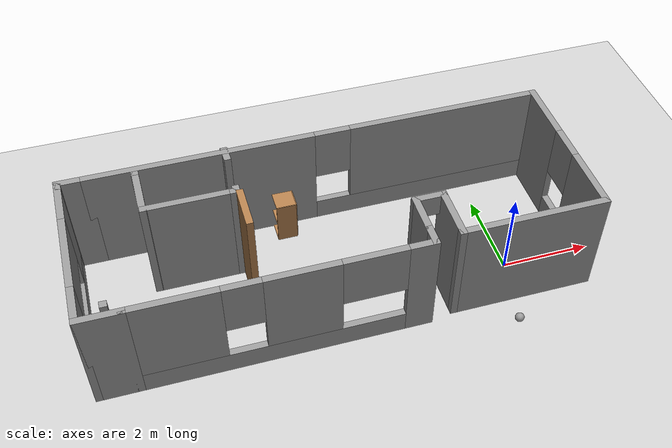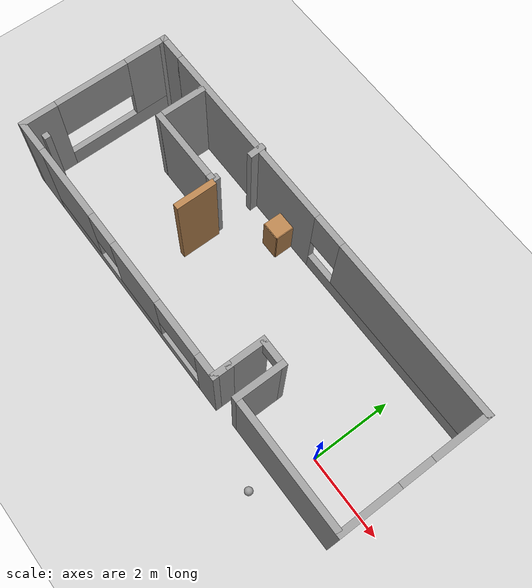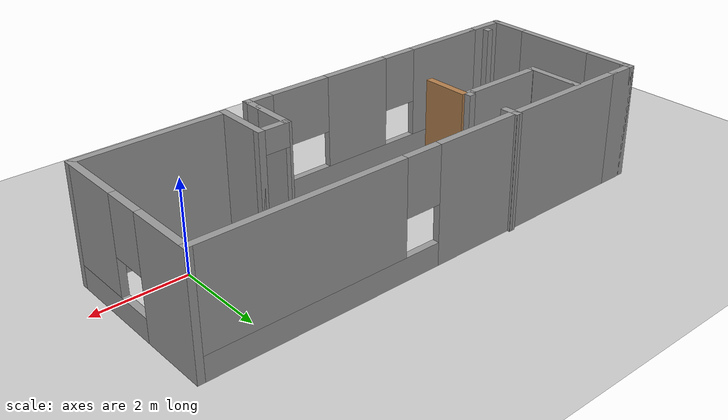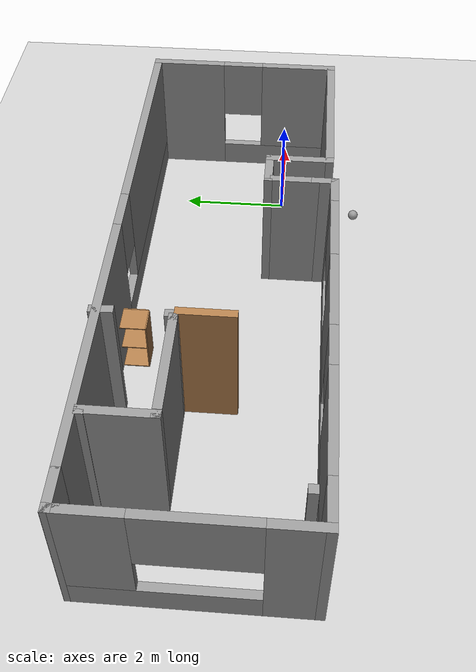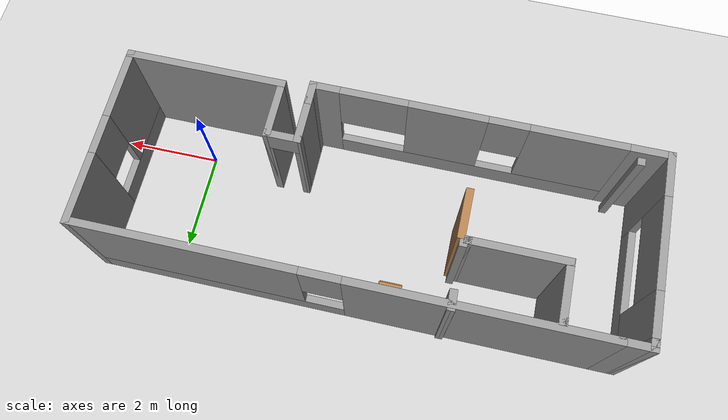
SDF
<sdf version="1.6">
 <world name="default">
  <plugin name="hello" filename="libhello.so"/>
  <light name="sun" type="directional">
   <pose>0 0 10 0 -0 0</pose>
   <diffuse>0.8 0.8 0.8 1</diffuse>
   <specular>0.1 0.1 0.1 1</specular>
   <attenuation>
    <range>1000</range>
    <constant>0.9</constant>
    <linear>0.01</linear>
    <quadratic>0.001</quadratic>
   </attenuation>
   <direction>-0.5 0.5 -1</direction>
  </light>
  <model name="ground_plane">
   <static>1</static>
   <link name="link">
    <collision name="collision">
     <geometry><plane><normal>0 0 1</normal><size>100 100</size></plane></geometry>
     <surface><friction><ode><mu>100</mu><mu2>50</mu2></ode></friction></surface>
    </collision>
    <visual name="visual">
     <cast_shadows>0</cast_shadows>
     <geometry><plane><normal>0 0 1</normal><size>100 100</size></plane></geometry>
     <material>
      <script><uri>file://media/materials/scripts/gazebo.material</uri><name>Gazebo/Grey</name></script>
     </material>
    </visual>
   </link>
  </model>
  <gravity>0 0 -9.8</gravity>
  <magnetic_field>6e-06 2.3e-05 -4.2e-05</magnetic_field>
  <atmosphere type="adiabatic"/>
  <physics name="default_physics" default="0" type="ode">
   <max_step_size>0.001</max_step_size>
   <real_time_factor>1</real_time_factor>
   <real_time_update_rate>1000</real_time_update_rate>
  </physics>
  <scene><ambient>0.4 0.4 0.4 1</ambient><background>0.7 0.7 0.7 1</background><shadows>1</shadows></scene>
  <spherical_coordinates>
   <surface_model>EARTH_WGS84</surface_model>
   <latitude_deg>0</latitude_deg>
   <longitude_deg>0</longitude_deg>
   <elevation>0</elevation>
   <heading_deg>0</heading_deg>
  </spherical_coordinates>
  <model name="coloredwall">
   <pose>-5.54358 0.999428 0 0 -0 0</pose>
   <link name="Wall_2">
    <collision name="Wall_2_Collision">
     <geometry><box><size>1 0.15 2.5</size></box></geometry>
     <pose>0 0 1.25 0 -0 0</pose>
    </collision>
    <visual name="Wall_2_Visual">
     <pose>0 0 1.25 0 -0 0</pose>
     <geometry><box><size>1 0.15 2.5</size></box></geometry>
     <material>
      <script><uri>file://media/materials/scripts/gazebo.material</uri><name>Gazebo/Wood</name></script>
      <ambient>1 1 1 1</ambient>
     </material>
     <meta><layer>0</layer></meta>
    </visual>
    <pose>0 0 0 0 -0 1.5708</pose>
   </link>
   <static>1</static>
  </model>
  <model name="cabinet">
   <static>1</static>
   <link name="cabinet_bottom_plate">
    <inertial>
     <pose>0 0 -1 0 -0 0</pose>
     <inertia><ixx>2.05</ixx><ixy>0</ixy><ixz>0</ixz><iyy>2.05</iyy><iyz>0</iyz><izz>2.05</izz></inertia>
     <mass>25</mass>
    </inertial>
    <collision name="cabinet_bottom_plate_geom">
     <pose>0 0 0.01 0 -0 0</pose>
     <geometry><box><size>0.45 0.45 0.02</size></box></geometry>
    </collision>
    <visual name="cabinet_bottom_plate_geom_visual">
     <pose>0 0 0.01 0 -0 0</pose>
     <geometry><box><size>0.45 0.45 0.02</size></box></geometry>
     <material>
      <script><uri>file://media/materials/scripts/gazebo.material</uri><name>Gazebo/Wood</name></script>
     </material>
    </visual>
    <collision name="cabinet_bottom_plate_geom_cabinet_back_plate">
     <pose>0.235 0 0.51 0 -0 0</pose>
     <geometry><box><size>0.02 0.45 1.02</size></box></geometry>
    </collision>
    <visual name="cabinet_bottom_plate_geom_cabinet_back_plate_visual">
     <pose>0.235 0 0.51 0 -0 0</pose>
     <geometry><box><size>0.02 0.45 1.02</size></box></geometry>
     <material>
      <script><uri>file://media/materials/scripts/gazebo.material</uri><name>Gazebo/Wood</name></script>
     </material>
    </visual>
    <collision name="cabinet_bottom_plate_geom_cabinet_left_plate">
     <pose>0 0.235 0.51 0 -0 0</pose>
     <geometry><box><size>0.45 0.02 1.02</size></box></geometry>
    </collision>
    <visual name="cabinet_bottom_plate_geom_cabinet_left_plate_visual">
     <pose>0 0.235 0.51 0 -0 0</pose>
     <geometry><box><size>0.45 0.02 1.02</size></box></geometry>
     <material>
      <script><uri>file://media/materials/scripts/gazebo.material</uri><name>Gazebo/Wood</name></script>
     </material>
    </visual>
    <collision name="cabinet_bottom_plate_geom_cabinet_middle_plate">
     <pose>0 0 0.51 0 -0 0</pose>
     <geometry><box><size>0.45 0.45 0.02</size></box></geometry>
    </collision>
    <visual name="cabinet_bottom_plate_geom_cabinet_middle_plate_visual">
     <pose>0 0 0.51 0 -0 0</pose>
     <geometry><box><size>0.45 0.45 0.02</size></box></geometry>
     <material>
      <script><uri>file://media/materials/scripts/gazebo.material</uri><name>Gazebo/Wood</name></script>
     </material>
    </visual>
    <collision name="cabinet_bottom_plate_geom_cabinet_right_plate">
     <pose>0 -0.235 0.51 0 -0 0</pose>
     <geometry><box><size>0.45 0.02 1.02</size></box></geometry>
    </collision>
    <visual name="cabinet_bottom_plate_geom_cabinet_right_plate_visual">
     <pose>0 -0.235 0.51 0 -0 0</pose>
     <geometry><box><size>0.45 0.02 1.02</size></box></geometry>
     <material>
      <script><uri>file://media/materials/scripts/gazebo.material</uri><name>Gazebo/Wood</name></script>
     </material>
    </visual>
    <collision name="cabinet_bottom_plate_geom_cabinet_top_plate">
     <pose>0 0 1.01 0 -0 0</pose>
     <geometry><box><size>0.45 0.45 0.02</size></box></geometry>
    </collision>
    <visual name="cabinet_bottom_plate_geom_cabinet_top_plate_visual">
     <pose>0 0 1.01 0 -0 0</pose>
     <geometry><box><size>0.45 0.45 0.02</size></box></geometry>
     <material>
      <script><uri>file://media/materials/scripts/gazebo.material</uri><name>Gazebo/Wood</name></script>
     </material>
    </visual>
   </link>
   <pose>-4.44524 2.41944 0 0 -0 0</pose>
  </model>
  <model name="basicbuilding">
   <link name="Wall_17">
    <pose>0.275 1.82353 0 0 -0 0</pose>
    <visual name="Wall_17_Visual_0">
     <pose>-2.6125 0 1.25 0 -0 0</pose>
     <geometry><box><size>5.025 0.15 2.5</size></box></geometry>
     <material>
      <script><uri>file://media/materials/scripts/gazebo.material</uri><name>Gazebo/Grey</name></script>
      <ambient>1 1 1 1</ambient>
      <shader type="pixel"/>
      <diffuse>0.7 0.7 0.7 1</diffuse>
      <specular>0.01 0.01 0.01 1</specular>
      <emissive>0 0 0 1</emissive>
     </material>
     <meta><layer>0</layer></meta>
    </visual>
    <visual name="Wall_17_Visual_1">
     <pose>2.5125 0 0.25 0 -0 0</pose>
     <geometry><box><size>5.225 0.15 0.5</size></box></geometry>
     <material>
      <script><uri>file://media/materials/scripts/gazebo.material</uri><name>Gazebo/Grey</name></script>
      <ambient>1 1 1 1</ambient>
      <shader type="pixel"/>
      <diffuse>0.7 0.7 0.7 1</diffuse>
      <specular>0.01 0.01 0.01 1</specular>
      <emissive>0 0 0 1</emissive>
     </material>
     <meta><layer>0</layer></meta>
    </visual>
    <visual name="Wall_17_Visual_2">
     <pose>2.9125 0 1.5 0 -0 0</pose>
     <geometry><box><size>4.425 0.15 2</size></box></geometry>
     <material>
      <script><uri>file://media/materials/scripts/gazebo.material</uri><name>Gazebo/Grey</name></script>
      <ambient>1 1 1 1</ambient>
      <shader type="pixel"/>
      <diffuse>0.7 0.7 0.7 1</diffuse>
      <specular>0.01 0.01 0.01 1</specular>
      <emissive>0 0 0 1</emissive>
     </material>
     <meta><layer>0</layer></meta>
    </visual>
    <visual name="Wall_17_Visual_3">
     <pose>0.3 0 1.9 0 -0 0</pose>
     <geometry><box><size>0.8 0.15 1.2</size></box></geometry>
     <material>
      <script><uri>file://media/materials/scripts/gazebo.material</uri><name>Gazebo/Grey</name></script>
      <ambient>1 1 1 1</ambient>
      <shader type="pixel"/>
      <diffuse>0.7 0.7 0.7 1</diffuse>
      <specular>0.01 0.01 0.01 1</specular>
      <emissive>0 0 0 1</emissive>
     </material>
     <meta><layer>0</layer></meta>
    </visual>
    <collision name="Wall_17_Collision_0">
     <pose>-2.6125 0 1.25 0 -0 0</pose>
     <geometry><box><size>5.025 0.15 2.5</size></box></geometry>
     <surface>
      <friction>
       <ode><mu>1</mu><mu2>1</mu2><fdir1>0 0 0</fdir1><slip1>0</slip1><slip2>0</slip2></ode>
       <torsional>
        <coefficient>1</coefficient>
        <patch_radius>0</patch_radius>
        <surface_radius>0</surface_radius>
        <use_patch_radius>1</use_patch_radius>
        <ode><slip>0</slip></ode>
       </torsional>
      </friction>
      <bounce><restitution_coefficient>0</restitution_coefficient><threshold>1e+06</threshold></bounce>
      <contact>
       <collide_without_contact>0</collide_without_contact>
       <collide_without_contact_bitmask>1</collide_without_contact_bitmask>
       <collide_bitmask>1</collide_bitmask>
       <ode>
        <soft_cfm>0</soft_cfm>
        <soft_erp>0.2</soft_erp>
        <kp>1e+13</kp>
        <kd>1</kd>
        <max_vel>0.01</max_vel>
        <min_depth>0</min_depth>
       </ode>
       <bullet>
        <split_impulse>1</split_impulse>
        <split_impulse_penetration_threshold>-0.01</split_impulse_penetration_threshold>
        <soft_cfm>0</soft_cfm>
        <soft_erp>0.2</soft_erp>
        <kp>1e+13</kp>
        <kd>1</kd>
       </bullet>
      </contact>
     </surface>
    </collision>
    <collision name="Wall_17_Collision_1">
     <pose>2.5125 0 0.25 0 -0 0</pose>
     <geometry><box><size>5.225 0.15 0.5</size></box></geometry>
     <surface>
      <friction>
       <ode><mu>1</mu><mu2>1</mu2><fdir1>0 0 0</fdir1><slip1>0</slip1><slip2>0</slip2></ode>
       <torsional>
        <coefficient>1</coefficient>
        <patch_radius>0</patch_radius>
        <surface_radius>0</surface_radius>
        <use_patch_radius>1</use_patch_radius>
        <ode><slip>0</slip></ode>
       </torsional>
      </friction>
      <bounce><restitution_coefficient>0</restitution_coefficient><threshold>1e+06</threshold></bounce>
      <contact>
       <collide_without_contact>0</collide_without_contact>
       <collide_without_contact_bitmask>1</collide_without_contact_bitmask>
       <collide_bitmask>1</collide_bitmask>
       <ode>
        <soft_cfm>0</soft_cfm>
        <soft_erp>0.2</soft_erp>
        <kp>1e+13</kp>
        <kd>1</kd>
        <max_vel>0.01</max_vel>
        <min_depth>0</min_depth>
       </ode>
       <bullet>
        <split_impulse>1</split_impulse>
        <split_impulse_penetration_threshold>-0.01</split_impulse_penetration_threshold>
        <soft_cfm>0</soft_cfm>
        <soft_erp>0.2</soft_erp>
        <kp>1e+13</kp>
        <kd>1</kd>
       </bullet>
      </contact>
     </surface>
    </collision>
    <collision name="Wall_17_Collision_2">
     <pose>2.9125 0 1.5 0 -0 0</pose>
     <geometry><box><size>4.425 0.15 2</size></box></geometry>
     <surface>
      <friction>
       <ode><mu>1</mu><mu2>1</mu2><fdir1>0 0 0</fdir1><slip1>0</slip1><slip2>0</slip2></ode>
       <torsional>
        <coefficient>1</coefficient>
        <patch_radius>0</patch_radius>
        <surface_radius>0</surface_radius>
        <use_patch_radius>1</use_patch_radius>
        <ode><slip>0</slip></ode>
       </torsional>
      </friction>
      <bounce><restitution_coefficient>0</restitution_coefficient><threshold>1e+06</threshold></bounce>
      <contact>
       <collide_without_contact>0</collide_without_contact>
       <collide_without_contact_bitmask>1</collide_without_contact_bitmask>
       <collide_bitmask>1</collide_bitmask>
       <ode>
        <soft_cfm>0</soft_cfm>
        <soft_erp>0.2</soft_erp>
        <kp>1e+13</kp>
        <kd>1</kd>
        <max_vel>0.01</max_vel>
        <min_depth>0</min_depth>
       </ode>
       <bullet>
        <split_impulse>1</split_impulse>
        <split_impulse_penetration_threshold>-0.01</split_impulse_penetration_threshold>
        <soft_cfm>0</soft_cfm>
        <soft_erp>0.2</soft_erp>
        <kp>1e+13</kp>
        <kd>1</kd>
       </bullet>
      </contact>
     </surface>
    </collision>
    <collision name="Wall_17_Collision_3">
     <pose>0.3 0 1.9 0 -0 0</pose>
     <geometry><box><size>0.8 0.15 1.2</size></box></geometry>
     <surface>
      <friction>
       <ode><mu>1</mu><mu2>1</mu2><fdir1>0 0 0</fdir1><slip1>0</slip1><slip2>0</slip2></ode>
       <torsional>
        <coefficient>1</coefficient>
        <patch_radius>0</patch_radius>
        <surface_radius>0</surface_radius>
        <use_patch_radius>1</use_patch_radius>
        <ode><slip>0</slip></ode>
       </torsional>
      </friction>
      <bounce><restitution_coefficient>0</restitution_coefficient><threshold>1e+06</threshold></bounce>
      <contact>
       <collide_without_contact>0</collide_without_contact>
       <collide_without_contact_bitmask>1</collide_without_contact_bitmask>
       <collide_bitmask>1</collide_bitmask>
       <ode>
        <soft_cfm>0</soft_cfm>
        <soft_erp>0.2</soft_erp>
        <kp>1e+13</kp>
        <kd>1</kd>
        <max_vel>0.01</max_vel>
        <min_depth>0</min_depth>
       </ode>
       <bullet>
        <split_impulse>1</split_impulse>
        <split_impulse_penetration_threshold>-0.01</split_impulse_penetration_threshold>
        <soft_cfm>0</soft_cfm>
        <soft_erp>0.2</soft_erp>
        <kp>1e+13</kp>
        <kd>1</kd>
       </bullet>
      </contact>
     </surface>
    </collision>
   </link>
   <link name="Wall_18">
    <pose>5.325 0.023531 0 0 0 -1.5708</pose>
    <visual name="Wall_18_Visual_0">
     <pose>-1.1475 0 1.25 0 -0 0</pose>
     <geometry><box><size>1.455 0.15 2.5</size></box></geometry>
     <material>
      <script><uri>file://media/materials/scripts/gazebo.material</uri><name>Gazebo/Grey</name></script>
      <ambient>1 1 1 1</ambient>
      <shader type="pixel"/>
      <diffuse>0.7 0.7 0.7 1</diffuse>
      <specular>0.01 0.01 0.01 1</specular>
      <emissive>0 0 0 1</emissive>
     </material>
     <meta><layer>0</layer></meta>
    </visual>
    <visual name="Wall_18_Visual_1">
     <pose>0.7275 0 0.25 0 -0 0</pose>
     <geometry><box><size>2.295 0.15 0.5</size></box></geometry>
     <material>
      <script><uri>file://media/materials/scripts/gazebo.material</uri><name>Gazebo/Grey</name></script>
      <ambient>1 1 1 1</ambient>
      <shader type="pixel"/>
      <diffuse>0.7 0.7 0.7 1</diffuse>
      <specular>0.01 0.01 0.01 1</specular>
      <emissive>0 0 0 1</emissive>
     </material>
     <meta><layer>0</layer></meta>
    </visual>
    <visual name="Wall_18_Visual_2">
     <pose>1.1275 0 1.5 0 -0 0</pose>
     <geometry><box><size>1.495 0.15 2</size></box></geometry>
     <material>
      <script><uri>file://media/materials/scripts/gazebo.material</uri><name>Gazebo/Grey</name></script>
      <ambient>1 1 1 1</ambient>
      <shader type="pixel"/>
      <diffuse>0.7 0.7 0.7 1</diffuse>
      <specular>0.01 0.01 0.01 1</specular>
      <emissive>0 0 0 1</emissive>
     </material>
     <meta><layer>0</layer></meta>
    </visual>
    <visual name="Wall_18_Visual_3">
     <pose>-0.02 0 1.9 0 -0 0</pose>
     <geometry><box><size>0.8 0.15 1.2</size></box></geometry>
     <material>
      <script><uri>file://media/materials/scripts/gazebo.material</uri><name>Gazebo/Grey</name></script>
      <ambient>1 1 1 1</ambient>
      <shader type="pixel"/>
      <diffuse>0.7 0.7 0.7 1</diffuse>
      <specular>0.01 0.01 0.01 1</specular>
      <emissive>0 0 0 1</emissive>
     </material>
     <meta><layer>0</layer></meta>
    </visual>
    <collision name="Wall_18_Collision_0">
     <pose>-1.1475 0 1.25 0 -0 0</pose>
     <geometry><box><size>1.455 0.15 2.5</size></box></geometry>
     <surface>
      <friction>
       <ode><mu>1</mu><mu2>1</mu2><fdir1>0 0 0</fdir1><slip1>0</slip1><slip2>0</slip2></ode>
       <torsional>
        <coefficient>1</coefficient>
        <patch_radius>0</patch_radius>
        <surface_radius>0</surface_radius>
        <use_patch_radius>1</use_patch_radius>
        <ode><slip>0</slip></ode>
       </torsional>
      </friction>
      <bounce><restitution_coefficient>0</restitution_coefficient><threshold>1e+06</threshold></bounce>
      <contact>
       <collide_without_contact>0</collide_without_contact>
       <collide_without_contact_bitmask>1</collide_without_contact_bitmask>
       <collide_bitmask>1</collide_bitmask>
       <ode>
        <soft_cfm>0</soft_cfm>
        <soft_erp>0.2</soft_erp>
        <kp>1e+13</kp>
        <kd>1</kd>
        <max_vel>0.01</max_vel>
        <min_depth>0</min_depth>
       </ode>
       <bullet>
        <split_impulse>1</split_impulse>
        <split_impulse_penetration_threshold>-0.01</split_impulse_penetration_threshold>
        <soft_cfm>0</soft_cfm>
        <soft_erp>0.2</soft_erp>
        <kp>1e+13</kp>
        <kd>1</kd>
       </bullet>
      </contact>
     </surface>
    </collision>
    <collision name="Wall_18_Collision_1">
     <pose>0.7275 0 0.25 0 -0 0</pose>
     <geometry><box><size>2.295 0.15 0.5</size></box></geometry>
     <surface>
      <friction>
       <ode><mu>1</mu><mu2>1</mu2><fdir1>0 0 0</fdir1><slip1>0</slip1><slip2>0</slip2></ode>
       <torsional>
        <coefficient>1</coefficient>
        <patch_radius>0</patch_radius>
        <surface_radius>0</surface_radius>
        <use_patch_radius>1</use_patch_radius>
        <ode><slip>0</slip></ode>
       </torsional>
      </friction>
      <bounce><restitution_coefficient>0</restitution_coefficient><threshold>1e+06</threshold></bounce>
      <contact>
       <collide_without_contact>0</collide_without_contact>
       <collide_without_contact_bitmask>1</collide_without_contact_bitmask>
       <collide_bitmask>1</collide_bitmask>
       <ode>
        <soft_cfm>0</soft_cfm>
        <soft_erp>0.2</soft_erp>
        <kp>1e+13</kp>
        <kd>1</kd>
        <max_vel>0.01</max_vel>
        <min_depth>0</min_depth>
       </ode>
       <bullet>
        <split_impulse>1</split_impulse>
        <split_impulse_penetration_threshold>-0.01</split_impulse_penetration_threshold>
        <soft_cfm>0</soft_cfm>
        <soft_erp>0.2</soft_erp>
        <kp>1e+13</kp>
        <kd>1</kd>
       </bullet>
      </contact>
     </surface>
    </collision>
    <collision name="Wall_18_Collision_2">
     <pose>1.1275 0 1.5 0 -0 0</pose>
     <geometry><box><size>1.495 0.15 2</size></box></geometry>
     <surface>
      <friction>
       <ode><mu>1</mu><mu2>1</mu2><fdir1>0 0 0</fdir1><slip1>0</slip1><slip2>0</slip2></ode>
       <torsional>
        <coefficient>1</coefficient>
        <patch_radius>0</patch_radius>
        <surface_radius>0</surface_radius>
        <use_patch_radius>1</use_patch_radius>
        <ode><slip>0</slip></ode>
       </torsional>
      </friction>
      <bounce><restitution_coefficient>0</restitution_coefficient><threshold>1e+06</threshold></bounce>
      <contact>
       <collide_without_contact>0</collide_without_contact>
       <collide_without_contact_bitmask>1</collide_without_contact_bitmask>
       <collide_bitmask>1</collide_bitmask>
       <ode>
        <soft_cfm>0</soft_cfm>
        <soft_erp>0.2</soft_erp>
        <kp>1e+13</kp>
        <kd>1</kd>
        <max_vel>0.01</max_vel>
        <min_depth>0</min_depth>
       </ode>
       <bullet>
        <split_impulse>1</split_impulse>
        <split_impulse_penetration_threshold>-0.01</split_impulse_penetration_threshold>
        <soft_cfm>0</soft_cfm>
        <soft_erp>0.2</soft_erp>
        <kp>1e+13</kp>
        <kd>1</kd>
       </bullet>
      </contact>
     </surface>
    </collision>
    <collision name="Wall_18_Collision_3">
     <pose>-0.02 0 1.9 0 -0 0</pose>
     <geometry><box><size>0.8 0.15 1.2</size></box></geometry>
     <surface>
      <friction>
       <ode><mu>1</mu><mu2>1</mu2><fdir1>0 0 0</fdir1><slip1>0</slip1><slip2>0</slip2></ode>
       <torsional>
        <coefficient>1</coefficient>
        <patch_radius>0</patch_radius>
        <surface_radius>0</surface_radius>
        <use_patch_radius>1</use_patch_radius>
        <ode><slip>0</slip></ode>
       </torsional>
      </friction>
      <bounce><restitution_coefficient>0</restitution_coefficient><threshold>1e+06</threshold></bounce>
      <contact>
       <collide_without_contact>0</collide_without_contact>
       <collide_without_contact_bitmask>1</collide_without_contact_bitmask>
       <collide_bitmask>1</collide_bitmask>
       <ode>
        <soft_cfm>0</soft_cfm>
        <soft_erp>0.2</soft_erp>
        <kp>1e+13</kp>
        <kd>1</kd>
        <max_vel>0.01</max_vel>
        <min_depth>0</min_depth>
       </ode>
       <bullet>
        <split_impulse>1</split_impulse>
        <split_impulse_penetration_threshold>-0.01</split_impulse_penetration_threshold>
        <soft_cfm>0</soft_cfm>
        <soft_erp>0.2</soft_erp>
        <kp>1e+13</kp>
        <kd>1</kd>
       </bullet>
      </contact>
     </surface>
    </collision>
   </link>
   <link name="Wall_19">
    <pose>3.775 -1.77647 0 0 -0 3.14159</pose>
    <visual name="Wall_19_Visual">
     <pose>0 0 1.25 0 -0 0</pose>
     <geometry><box><size>3.25 0.15 2.5</size></box></geometry>
     <material>
      <script><uri>file://media/materials/scripts/gazebo.material</uri><name>Gazebo/Grey</name></script>
      <ambient>1 1 1 1</ambient>
      <shader type="pixel"/>
      <diffuse>0.7 0.7 0.7 1</diffuse>
      <specular>0.01 0.01 0.01 1</specular>
      <emissive>0 0 0 1</emissive>
     </material>
     <meta><layer>0</layer></meta>
    </visual>
    <collision name="Wall_19_Collision">
     <pose>0 0 1.25 0 -0 0</pose>
     <geometry><box><size>3.25 0.15 2.5</size></box></geometry>
     <surface>
      <friction>
       <ode><mu>1</mu><mu2>1</mu2><fdir1>0 0 0</fdir1><slip1>0</slip1><slip2>0</slip2></ode>
       <torsional>
        <coefficient>1</coefficient>
        <patch_radius>0</patch_radius>
        <surface_radius>0</surface_radius>
        <use_patch_radius>1</use_patch_radius>
        <ode><slip>0</slip></ode>
       </torsional>
      </friction>
      <bounce><restitution_coefficient>0</restitution_coefficient><threshold>1e+06</threshold></bounce>
      <contact>
       <collide_without_contact>0</collide_without_contact>
       <collide_without_contact_bitmask>1</collide_without_contact_bitmask>
       <collide_bitmask>1</collide_bitmask>
       <ode>
        <soft_cfm>0</soft_cfm>
        <soft_erp>0.2</soft_erp>
        <kp>1e+13</kp>
        <kd>1</kd>
        <max_vel>0.01</max_vel>
        <min_depth>0</min_depth>
       </ode>
       <bullet>
        <split_impulse>1</split_impulse>
        <split_impulse_penetration_threshold>-0.01</split_impulse_penetration_threshold>
        <soft_cfm>0</soft_cfm>
        <soft_erp>0.2</soft_erp>
        <kp>1e+13</kp>
        <kd>1</kd>
       </bullet>
      </contact>
     </surface>
    </collision>
   </link>
   <link name="Wall_20">
    <pose>2.225 -1.22647 0 0 -0 1.5708</pose>
    <visual name="Wall_20_Visual">
     <pose>0 0 1.25 0 -0 0</pose>
     <geometry><box><size>1.25 0.15 2.5</size></box></geometry>
     <material>
      <script><uri>file://media/materials/scripts/gazebo.material</uri><name>Gazebo/Grey</name></script>
      <ambient>1 1 1 1</ambient>
      <shader type="pixel"/>
      <diffuse>0.7 0.7 0.7 1</diffuse>
      <specular>0.01 0.01 0.01 1</specular>
      <emissive>0 0 0 1</emissive>
     </material>
     <meta><layer>0</layer></meta>
    </visual>
    <collision name="Wall_20_Collision">
     <pose>0 0 1.25 0 -0 0</pose>
     <geometry><box><size>1.25 0.15 2.5</size></box></geometry>
     <surface>
      <friction>
       <ode><mu>1</mu><mu2>1</mu2><fdir1>0 0 0</fdir1><slip1>0</slip1><slip2>0</slip2></ode>
       <torsional>
        <coefficient>1</coefficient>
        <patch_radius>0</patch_radius>
        <surface_radius>0</surface_radius>
        <use_patch_radius>1</use_patch_radius>
        <ode><slip>0</slip></ode>
       </torsional>
      </friction>
      <bounce><restitution_coefficient>0</restitution_coefficient><threshold>1e+06</threshold></bounce>
      <contact>
       <collide_without_contact>0</collide_without_contact>
       <collide_without_contact_bitmask>1</collide_without_contact_bitmask>
       <collide_bitmask>1</collide_bitmask>
       <ode>
        <soft_cfm>0</soft_cfm>
        <soft_erp>0.2</soft_erp>
        <kp>1e+13</kp>
        <kd>1</kd>
        <max_vel>0.01</max_vel>
        <min_depth>0</min_depth>
       </ode>
       <bullet>
        <split_impulse>1</split_impulse>
        <split_impulse_penetration_threshold>-0.01</split_impulse_penetration_threshold>
        <soft_cfm>0</soft_cfm>
        <soft_erp>0.2</soft_erp>
        <kp>1e+13</kp>
        <kd>1</kd>
       </bullet>
      </contact>
     </surface>
    </collision>
   </link>
   <link name="Wall_21">
    <pose>1.925 -0.676469 0 0 -0 3.14159</pose>
    <visual name="Wall_21_Visual_0">
     <pose>-0.33 0 1.25 0 -0 0</pose>
     <geometry><box><size>0.09 0.15 2.5</size></box></geometry>
     <material>
      <script><uri>file://media/materials/scripts/gazebo.material</uri><name>Gazebo/Grey</name></script>
      <ambient>1 1 1 1</ambient>
      <shader type="pixel"/>
      <diffuse>0.7 0.7 0.7 1</diffuse>
      <specular>0.01 0.01 0.01 1</specular>
      <emissive>0 0 0 1</emissive>
     </material>
     <meta><layer>0</layer></meta>
    </visual>
    <visual name="Wall_21_Visual_1">
     <pose>0.345 0 1.25 0 -0 0</pose>
     <geometry><box><size>0.06 0.15 2.5</size></box></geometry>
     <material>
      <script><uri>file://media/materials/scripts/gazebo.material</uri><name>Gazebo/Grey</name></script>
      <ambient>1 1 1 1</ambient>
      <shader type="pixel"/>
      <diffuse>0.7 0.7 0.7 1</diffuse>
      <specular>0.01 0.01 0.01 1</specular>
      <emissive>0 0 0 1</emissive>
     </material>
     <meta><layer>0</layer></meta>
    </visual>
    <visual name="Wall_21_Visual_2">
     <pose>0.015 0 2.25 0 -0 0</pose>
     <geometry><box><size>0.6 0.15 0.5</size></box></geometry>
     <material>
      <script><uri>file://media/materials/scripts/gazebo.material</uri><name>Gazebo/Grey</name></script>
      <ambient>1 1 1 1</ambient>
      <shader type="pixel"/>
      <diffuse>0.7 0.7 0.7 1</diffuse>
      <specular>0.01 0.01 0.01 1</specular>
      <emissive>0 0 0 1</emissive>
     </material>
     <meta><layer>0</layer></meta>
    </visual>
    <collision name="Wall_21_Collision_0">
     <pose>-0.33 0 1.25 0 -0 0</pose>
     <geometry><box><size>0.09 0.15 2.5</size></box></geometry>
     <surface>
      <friction>
       <ode><mu>1</mu><mu2>1</mu2><fdir1>0 0 0</fdir1><slip1>0</slip1><slip2>0</slip2></ode>
       <torsional>
        <coefficient>1</coefficient>
        <patch_radius>0</patch_radius>
        <surface_radius>0</surface_radius>
        <use_patch_radius>1</use_patch_radius>
        <ode><slip>0</slip></ode>
       </torsional>
      </friction>
      <bounce><restitution_coefficient>0</restitution_coefficient><threshold>1e+06</threshold></bounce>
      <contact>
       <collide_without_contact>0</collide_without_contact>
       <collide_without_contact_bitmask>1</collide_without_contact_bitmask>
       <collide_bitmask>1</collide_bitmask>
       <ode>
        <soft_cfm>0</soft_cfm>
        <soft_erp>0.2</soft_erp>
        <kp>1e+13</kp>
        <kd>1</kd>
        <max_vel>0.01</max_vel>
        <min_depth>0</min_depth>
       </ode>
       <bullet>
        <split_impulse>1</split_impulse>
        <split_impulse_penetration_threshold>-0.01</split_impulse_penetration_threshold>
        <soft_cfm>0</soft_cfm>
        <soft_erp>0.2</soft_erp>
        <kp>1e+13</kp>
        <kd>1</kd>
       </bullet>
      </contact>
     </surface>
    </collision>
    <collision name="Wall_21_Collision_1">
     <pose>0.345 0 1.25 0 -0 0</pose>
     <geometry><box><size>0.06 0.15 2.5</size></box></geometry>
     <surface>
      <friction>
       <ode><mu>1</mu><mu2>1</mu2><fdir1>0 0 0</fdir1><slip1>0</slip1><slip2>0</slip2></ode>
       <torsional>
        <coefficient>1</coefficient>
        <patch_radius>0</patch_radius>
        <surface_radius>0</surface_radius>
        <use_patch_radius>1</use_patch_radius>
        <ode><slip>0</slip></ode>
       </torsional>
      </friction>
      <bounce><restitution_coefficient>0</restitution_coefficient><threshold>1e+06</threshold></bounce>
      <contact>
       <collide_without_contact>0</collide_without_contact>
       <collide_without_contact_bitmask>1</collide_without_contact_bitmask>
       <collide_bitmask>1</collide_bitmask>
       <ode>
        <soft_cfm>0</soft_cfm>
        <soft_erp>0.2</soft_erp>
        <kp>1e+13</kp>
        <kd>1</kd>
        <max_vel>0.01</max_vel>
        <min_depth>0</min_depth>
       </ode>
       <bullet>
        <split_impulse>1</split_impulse>
        <split_impulse_penetration_threshold>-0.01</split_impulse_penetration_threshold>
        <soft_cfm>0</soft_cfm>
        <soft_erp>0.2</soft_erp>
        <kp>1e+13</kp>
        <kd>1</kd>
       </bullet>
      </contact>
     </surface>
    </collision>
    <collision name="Wall_21_Collision_2">
     <pose>0.015 0 2.25 0 -0 0</pose>
     <geometry><box><size>0.6 0.15 0.5</size></box></geometry>
     <surface>
      <friction>
       <ode><mu>1</mu><mu2>1</mu2><fdir1>0 0 0</fdir1><slip1>0</slip1><slip2>0</slip2></ode>
       <torsional>
        <coefficient>1</coefficient>
        <patch_radius>0</patch_radius>
        <surface_radius>0</surface_radius>
        <use_patch_radius>1</use_patch_radius>
        <ode><slip>0</slip></ode>
       </torsional>
      </friction>
      <bounce><restitution_coefficient>0</restitution_coefficient><threshold>1e+06</threshold></bounce>
      <contact>
       <collide_without_contact>0</collide_without_contact>
       <collide_without_contact_bitmask>1</collide_without_contact_bitmask>
       <collide_bitmask>1</collide_bitmask>
       <ode>
        <soft_cfm>0</soft_cfm>
        <soft_erp>0.2</soft_erp>
        <kp>1e+13</kp>
        <kd>1</kd>
        <max_vel>0.01</max_vel>
        <min_depth>0</min_depth>
       </ode>
       <bullet>
        <split_impulse>1</split_impulse>
        <split_impulse_penetration_threshold>-0.01</split_impulse_penetration_threshold>
        <soft_cfm>0</soft_cfm>
        <soft_erp>0.2</soft_erp>
        <kp>1e+13</kp>
        <kd>1</kd>
       </bullet>
      </contact>
     </surface>
    </collision>
   </link>
   <link name="Wall_22">
    <pose>1.625 -1.10147 0 0 0 -1.5708</pose>
    <visual name="Wall_22_Visual">
     <pose>0 0 1.25 0 -0 0</pose>
     <geometry><box><size>1 0.15 2.5</size></box></geometry>
     <material>
      <script><uri>file://media/materials/scripts/gazebo.material</uri><name>Gazebo/Grey</name></script>
      <ambient>1 1 1 1</ambient>
      <shader type="pixel"/>
      <diffuse>0.7 0.7 0.7 1</diffuse>
      <specular>0.01 0.01 0.01 1</specular>
      <emissive>0 0 0 1</emissive>
     </material>
     <meta><layer>0</layer></meta>
    </visual>
    <collision name="Wall_22_Collision">
     <pose>0 0 1.25 0 -0 0</pose>
     <geometry><box><size>1 0.15 2.5</size></box></geometry>
     <surface>
      <friction>
       <ode><mu>1</mu><mu2>1</mu2><fdir1>0 0 0</fdir1><slip1>0</slip1><slip2>0</slip2></ode>
       <torsional>
        <coefficient>1</coefficient>
        <patch_radius>0</patch_radius>
        <surface_radius>0</surface_radius>
        <use_patch_radius>1</use_patch_radius>
        <ode><slip>0</slip></ode>
       </torsional>
      </friction>
      <bounce><restitution_coefficient>0</restitution_coefficient><threshold>1e+06</threshold></bounce>
      <contact>
       <collide_without_contact>0</collide_without_contact>
       <collide_without_contact_bitmask>1</collide_without_contact_bitmask>
       <collide_bitmask>1</collide_bitmask>
       <ode>
        <soft_cfm>0</soft_cfm>
        <soft_erp>0.2</soft_erp>
        <kp>1e+13</kp>
        <kd>1</kd>
        <max_vel>0.01</max_vel>
        <min_depth>0</min_depth>
       </ode>
       <bullet>
        <split_impulse>1</split_impulse>
        <split_impulse_penetration_threshold>-0.01</split_impulse_penetration_threshold>
        <soft_cfm>0</soft_cfm>
        <soft_erp>0.2</soft_erp>
        <kp>1e+13</kp>
        <kd>1</kd>
       </bullet>
      </contact>
     </surface>
    </collision>
   </link>
   <link name="Wall_23">
    <pose>1.625 -1.70147 0 0 0 -1.5708</pose>
    <visual name="Wall_23_Visual">
     <pose>0 0 1.25 0 -0 0</pose>
     <geometry><box><size>0.5 0.15 2.5</size></box></geometry>
     <material>
      <script><uri>file://media/materials/scripts/gazebo.material</uri><name>Gazebo/Grey</name></script>
      <ambient>1 1 1 1</ambient>
      <shader type="pixel"/>
      <diffuse>0.7 0.7 0.7 1</diffuse>
      <specular>0.01 0.01 0.01 1</specular>
      <emissive>0 0 0 1</emissive>
     </material>
     <meta><layer>0</layer></meta>
    </visual>
    <collision name="Wall_23_Collision">
     <pose>0 0 1.25 0 -0 0</pose>
     <geometry><box><size>0.5 0.15 2.5</size></box></geometry>
     <surface>
      <friction>
       <ode><mu>1</mu><mu2>1</mu2><fdir1>0 0 0</fdir1><slip1>0</slip1><slip2>0</slip2></ode>
       <torsional>
        <coefficient>1</coefficient>
        <patch_radius>0</patch_radius>
        <surface_radius>0</surface_radius>
        <use_patch_radius>1</use_patch_radius>
        <ode><slip>0</slip></ode>
       </torsional>
      </friction>
      <bounce><restitution_coefficient>0</restitution_coefficient><threshold>1e+06</threshold></bounce>
      <contact>
       <collide_without_contact>0</collide_without_contact>
       <collide_without_contact_bitmask>1</collide_without_contact_bitmask>
       <collide_bitmask>1</collide_bitmask>
       <ode>
        <soft_cfm>0</soft_cfm>
        <soft_erp>0.2</soft_erp>
        <kp>1e+13</kp>
        <kd>1</kd>
        <max_vel>0.01</max_vel>
        <min_depth>0</min_depth>
       </ode>
       <bullet>
        <split_impulse>1</split_impulse>
        <split_impulse_penetration_threshold>-0.01</split_impulse_penetration_threshold>
        <soft_cfm>0</soft_cfm>
        <soft_erp>0.2</soft_erp>
        <kp>1e+13</kp>
        <kd>1</kd>
       </bullet>
      </contact>
     </surface>
    </collision>
   </link>
   <link name="Wall_24">
    <pose>-1.425 -1.87647 0 0 -0 3.14159</pose>
    <visual name="Wall_24_Visual_0">
     <pose>-2.8175 0 1.25 0 -0 0</pose>
     <geometry><box><size>0.615 0.15 2.5</size></box></geometry>
     <material>
      <script><uri>file://media/materials/scripts/gazebo.material</uri><name>Gazebo/Grey</name></script>
      <ambient>1 1 1 1</ambient>
      <shader type="pixel"/>
      <diffuse>0.7 0.7 0.7 1</diffuse>
      <specular>0.01 0.01 0.01 1</specular>
      <emissive>0 0 0 1</emissive>
     </material>
     <meta><layer>0</layer></meta>
    </visual>
    <visual name="Wall_24_Visual_1">
     <pose>0.3075 0 0.25 0 -0 0</pose>
     <geometry><box><size>5.635 0.15 0.5</size></box></geometry>
     <material>
      <script><uri>file://media/materials/scripts/gazebo.material</uri><name>Gazebo/Grey</name></script>
      <ambient>1 1 1 1</ambient>
      <shader type="pixel"/>
      <diffuse>0.7 0.7 0.7 1</diffuse>
      <specular>0.01 0.01 0.01 1</specular>
      <emissive>0 0 0 1</emissive>
     </material>
     <meta><layer>0</layer></meta>
    </visual>
    <visual name="Wall_24_Visual_2">
     <pose>-0.365 0 1.5 0 -0 0</pose>
     <geometry><box><size>1.57 0.15 2</size></box></geometry>
     <material>
      <script><uri>file://media/materials/scripts/gazebo.material</uri><name>Gazebo/Grey</name></script>
      <ambient>1 1 1 1</ambient>
      <shader type="pixel"/>
      <diffuse>0.7 0.7 0.7 1</diffuse>
      <specular>0.01 0.01 0.01 1</specular>
      <emissive>0 0 0 1</emissive>
     </material>
     <meta><layer>0</layer></meta>
    </visual>
    <visual name="Wall_24_Visual_3">
     <pose>2.1725 0 1.5 0 -0 0</pose>
     <geometry><box><size>1.905 0.15 2</size></box></geometry>
     <material>
      <script><uri>file://media/materials/scripts/gazebo.material</uri><name>Gazebo/Grey</name></script>
      <ambient>1 1 1 1</ambient>
      <shader type="pixel"/>
      <diffuse>0.7 0.7 0.7 1</diffuse>
      <specular>0.01 0.01 0.01 1</specular>
      <emissive>0 0 0 1</emissive>
     </material>
     <meta><layer>0</layer></meta>
    </visual>
    <visual name="Wall_24_Visual_4">
     <pose>-1.83 0 1.9 0 -0 0</pose>
     <geometry><box><size>1.36 0.15 1.2</size></box></geometry>
     <material>
      <script><uri>file://media/materials/scripts/gazebo.material</uri><name>Gazebo/Grey</name></script>
      <ambient>1 1 1 1</ambient>
      <shader type="pixel"/>
      <diffuse>0.7 0.7 0.7 1</diffuse>
      <specular>0.01 0.01 0.01 1</specular>
      <emissive>0 0 0 1</emissive>
     </material>
     <meta><layer>0</layer></meta>
    </visual>
    <visual name="Wall_24_Visual_5">
     <pose>0.82 0 1.9 0 -0 0</pose>
     <geometry><box><size>0.8 0.15 1.2</size></box></geometry>
     <material>
      <script><uri>file://media/materials/scripts/gazebo.material</uri><name>Gazebo/Grey</name></script>
      <ambient>1 1 1 1</ambient>
      <shader type="pixel"/>
      <diffuse>0.7 0.7 0.7 1</diffuse>
      <specular>0.01 0.01 0.01 1</specular>
      <emissive>0 0 0 1</emissive>
     </material>
     <meta><layer>0</layer></meta>
    </visual>
    <collision name="Wall_24_Collision_0">
     <pose>-2.8175 0 1.25 0 -0 0</pose>
     <geometry><box><size>0.615 0.15 2.5</size></box></geometry>
     <surface>
      <friction>
       <ode><mu>1</mu><mu2>1</mu2><fdir1>0 0 0</fdir1><slip1>0</slip1><slip2>0</slip2></ode>
       <torsional>
        <coefficient>1</coefficient>
        <patch_radius>0</patch_radius>
        <surface_radius>0</surface_radius>
        <use_patch_radius>1</use_patch_radius>
        <ode><slip>0</slip></ode>
       </torsional>
      </friction>
      <bounce><restitution_coefficient>0</restitution_coefficient><threshold>1e+06</threshold></bounce>
      <contact>
       <collide_without_contact>0</collide_without_contact>
       <collide_without_contact_bitmask>1</collide_without_contact_bitmask>
       <collide_bitmask>1</collide_bitmask>
       <ode>
        <soft_cfm>0</soft_cfm>
        <soft_erp>0.2</soft_erp>
        <kp>1e+13</kp>
        <kd>1</kd>
        <max_vel>0.01</max_vel>
        <min_depth>0</min_depth>
       </ode>
       <bullet>
        <split_impulse>1</split_impulse>
        <split_impulse_penetration_threshold>-0.01</split_impulse_penetration_threshold>
        <soft_cfm>0</soft_cfm>
        <soft_erp>0.2</soft_erp>
        <kp>1e+13</kp>
        <kd>1</kd>
       </bullet>
      </contact>
     </surface>
    </collision>
    <collision name="Wall_24_Collision_1">
     <pose>0.3075 0 0.25 0 -0 0</pose>
     <geometry><box><size>5.635 0.15 0.5</size></box></geometry>
     <surface>
      <friction>
       <ode><mu>1</mu><mu2>1</mu2><fdir1>0 0 0</fdir1><slip1>0</slip1><slip2>0</slip2></ode>
       <torsional>
        <coefficient>1</coefficient>
        <patch_radius>0</patch_radius>
        <surface_radius>0</surface_radius>
        <use_patch_radius>1</use_patch_radius>
        <ode><slip>0</slip></ode>
       </torsional>
      </friction>
      <bounce><restitution_coefficient>0</restitution_coefficient><threshold>1e+06</threshold></bounce>
      <contact>
       <collide_without_contact>0</collide_without_contact>
       <collide_without_contact_bitmask>1</collide_without_contact_bitmask>
       <collide_bitmask>1</collide_bitmask>
       <ode>
        <soft_cfm>0</soft_cfm>
        <soft_erp>0.2</soft_erp>
        <kp>1e+13</kp>
        <kd>1</kd>
        <max_vel>0.01</max_vel>
        <min_depth>0</min_depth>
       </ode>
       <bullet>
        <split_impulse>1</split_impulse>
        <split_impulse_penetration_threshold>-0.01</split_impulse_penetration_threshold>
        <soft_cfm>0</soft_cfm>
        <soft_erp>0.2</soft_erp>
        <kp>1e+13</kp>
        <kd>1</kd>
       </bullet>
      </contact>
     </surface>
    </collision>
    <collision name="Wall_24_Collision_2">
     <pose>-0.365 0 1.5 0 -0 0</pose>
     <geometry><box><size>1.57 0.15 2</size></box></geometry>
     <surface>
      <friction>
       <ode><mu>1</mu><mu2>1</mu2><fdir1>0 0 0</fdir1><slip1>0</slip1><slip2>0</slip2></ode>
       <torsional>
        <coefficient>1</coefficient>
        <patch_radius>0</patch_radius>
        <surface_radius>0</surface_radius>
        <use_patch_radius>1</use_patch_radius>
        <ode><slip>0</slip></ode>
       </torsional>
      </friction>
      <bounce><restitution_coefficient>0</restitution_coefficient><threshold>1e+06</threshold></bounce>
      <contact>
       <collide_without_contact>0</collide_without_contact>
       <collide_without_contact_bitmask>1</collide_without_contact_bitmask>
       <collide_bitmask>1</collide_bitmask>
       <ode>
        <soft_cfm>0</soft_cfm>
        <soft_erp>0.2</soft_erp>
        <kp>1e+13</kp>
        <kd>1</kd>
        <max_vel>0.01</max_vel>
        <min_depth>0</min_depth>
       </ode>
       <bullet>
        <split_impulse>1</split_impulse>
        <split_impulse_penetration_threshold>-0.01</split_impulse_penetration_threshold>
        <soft_cfm>0</soft_cfm>
        <soft_erp>0.2</soft_erp>
        <kp>1e+13</kp>
        <kd>1</kd>
       </bullet>
      </contact>
     </surface>
    </collision>
    <collision name="Wall_24_Collision_3">
     <pose>2.1725 0 1.5 0 -0 0</pose>
     <geometry><box><size>1.905 0.15 2</size></box></geometry>
     <surface>
      <friction>
       <ode><mu>1</mu><mu2>1</mu2><fdir1>0 0 0</fdir1><slip1>0</slip1><slip2>0</slip2></ode>
       <torsional>
        <coefficient>1</coefficient>
        <patch_radius>0</patch_radius>
        <surface_radius>0</surface_radius>
        <use_patch_radius>1</use_patch_radius>
        <ode><slip>0</slip></ode>
       </torsional>
      </friction>
      <bounce><restitution_coefficient>0</restitution_coefficient><threshold>1e+06</threshold></bounce>
      <contact>
       <collide_without_contact>0</collide_without_contact>
       <collide_without_contact_bitmask>1</collide_without_contact_bitmask>
       <collide_bitmask>1</collide_bitmask>
       <ode>
        <soft_cfm>0</soft_cfm>
        <soft_erp>0.2</soft_erp>
        <kp>1e+13</kp>
        <kd>1</kd>
        <max_vel>0.01</max_vel>
        <min_depth>0</min_depth>
       </ode>
       <bullet>
        <split_impulse>1</split_impulse>
        <split_impulse_penetration_threshold>-0.01</split_impulse_penetration_threshold>
        <soft_cfm>0</soft_cfm>
        <soft_erp>0.2</soft_erp>
        <kp>1e+13</kp>
        <kd>1</kd>
       </bullet>
      </contact>
     </surface>
    </collision>
    <collision name="Wall_24_Collision_5">
     <pose>0.82 0 1.9 0 -0 0</pose>
     <geometry><box><size>0.8 0.15 1.2</size></box></geometry>
     <surface>
      <friction>
       <ode><mu>1</mu><mu2>1</mu2><fdir1>0 0 0</fdir1><slip1>0</slip1><slip2>0</slip2></ode>
       <torsional>
        <coefficient>1</coefficient>
        <patch_radius>0</patch_radius>
        <surface_radius>0</surface_radius>
        <use_patch_radius>1</use_patch_radius>
        <ode><slip>0</slip></ode>
       </torsional>
      </friction>
      <bounce><restitution_coefficient>0</restitution_coefficient><threshold>1e+06</threshold></bounce>
      <contact>
       <collide_without_contact>0</collide_without_contact>
       <collide_without_contact_bitmask>1</collide_without_contact_bitmask>
       <collide_bitmask>1</collide_bitmask>
       <ode>
        <soft_cfm>0</soft_cfm>
        <soft_erp>0.2</soft_erp>
        <kp>1e+13</kp>
        <kd>1</kd>
        <max_vel>0.01</max_vel>
        <min_depth>0</min_depth>
       </ode>
       <bullet>
        <split_impulse>1</split_impulse>
        <split_impulse_penetration_threshold>-0.01</split_impulse_penetration_threshold>
        <soft_cfm>0</soft_cfm>
        <soft_erp>0.2</soft_erp>
        <kp>1e+13</kp>
        <kd>1</kd>
       </bullet>
      </contact>
     </surface>
    </collision>
    <collision name="Wall_24_Collision_4">
     <pose>-1.83 0 1.9 0 -0 0</pose>
     <geometry><box><size>1.36 0.15 1.2</size></box></geometry>
     <surface>
      <friction>
       <ode><mu>1</mu><mu2>1</mu2><fdir1>0 0 0</fdir1><slip1>0</slip1><slip2>0</slip2></ode>
       <torsional>
        <coefficient>1</coefficient>
        <patch_radius>0</patch_radius>
        <surface_radius>0</surface_radius>
        <use_patch_radius>1</use_patch_radius>
        <ode><slip>0</slip></ode>
       </torsional>
      </friction>
      <bounce><restitution_coefficient>0</restitution_coefficient><threshold>1e+06</threshold></bounce>
      <contact>
       <collide_without_contact>0</collide_without_contact>
       <collide_without_contact_bitmask>1</collide_without_contact_bitmask>
       <collide_bitmask>1</collide_bitmask>
       <ode>
        <soft_cfm>0</soft_cfm>
        <soft_erp>0.2</soft_erp>
        <kp>1e+13</kp>
        <kd>1</kd>
        <max_vel>0.01</max_vel>
        <min_depth>0</min_depth>
       </ode>
       <bullet>
        <split_impulse>1</split_impulse>
        <split_impulse_penetration_threshold>-0.01</split_impulse_penetration_threshold>
        <soft_cfm>0</soft_cfm>
        <soft_erp>0.2</soft_erp>
        <kp>1e+13</kp>
        <kd>1</kd>
       </bullet>
      </contact>
     </surface>
    </collision>
   </link>
   <link name="Wall_25">
    <pose>-4.475 -1.87647 0 0 -0 0</pose>
    <visual name="Wall_25_Visual">
     <pose>0 0 1.25 0 -0 0</pose>
     <geometry><box><size>0.15 0.15 2.5</size></box></geometry>
     <material>
      <script><uri>file://media/materials/scripts/gazebo.material</uri><name>Gazebo/Grey</name></script>
      <ambient>1 1 1 1</ambient>
      <shader type="pixel"/>
      <diffuse>0.7 0.7 0.7 1</diffuse>
      <specular>0.01 0.01 0.01 1</specular>
      <emissive>0 0 0 1</emissive>
     </material>
     <meta><layer>0</layer></meta>
    </visual>
    <collision name="Wall_25_Collision">
     <pose>0 0 1.25 0 -0 0</pose>
     <geometry><box><size>0.15 0.15 2.5</size></box></geometry>
     <surface>
      <friction>
       <ode><mu>1</mu><mu2>1</mu2><fdir1>0 0 0</fdir1><slip1>0</slip1><slip2>0</slip2></ode>
       <torsional>
        <coefficient>1</coefficient>
        <patch_radius>0</patch_radius>
        <surface_radius>0</surface_radius>
        <use_patch_radius>1</use_patch_radius>
        <ode><slip>0</slip></ode>
       </torsional>
      </friction>
      <bounce><restitution_coefficient>0</restitution_coefficient><threshold>1e+06</threshold></bounce>
      <contact>
       <collide_without_contact>0</collide_without_contact>
       <collide_without_contact_bitmask>1</collide_without_contact_bitmask>
       <collide_bitmask>1</collide_bitmask>
       <ode>
        <soft_cfm>0</soft_cfm>
        <soft_erp>0.2</soft_erp>
        <kp>1e+13</kp>
        <kd>1</kd>
        <max_vel>0.01</max_vel>
        <min_depth>0</min_depth>
       </ode>
       <bullet>
        <split_impulse>1</split_impulse>
        <split_impulse_penetration_threshold>-0.01</split_impulse_penetration_threshold>
        <soft_cfm>0</soft_cfm>
        <soft_erp>0.2</soft_erp>
        <kp>1e+13</kp>
        <kd>1</kd>
       </bullet>
      </contact>
     </surface>
    </collision>
   </link>
   <link name="Wall_26">
    <pose>-4.9 -1.87647 0 0 -0 3.14159</pose>
    <visual name="Wall_26_Visual">
     <pose>0 0 1.25 0 -0 0</pose>
     <geometry><box><size>1 0.15 2.5</size></box></geometry>
     <material>
      <script><uri>file://media/materials/scripts/gazebo.material</uri><name>Gazebo/Grey</name></script>
      <ambient>1 1 1 1</ambient>
      <shader type="pixel"/>
      <diffuse>0.7 0.7 0.7 1</diffuse>
      <specular>0.01 0.01 0.01 1</specular>
      <emissive>0 0 0 1</emissive>
     </material>
     <meta><layer>0</layer></meta>
    </visual>
    <collision name="Wall_26_Collision">
     <pose>0 0 1.25 0 -0 0</pose>
     <geometry><box><size>1 0.15 2.5</size></box></geometry>
     <surface>
      <friction>
       <ode><mu>1</mu><mu2>1</mu2><fdir1>0 0 0</fdir1><slip1>0</slip1><slip2>0</slip2></ode>
       <torsional>
        <coefficient>1</coefficient>
        <patch_radius>0</patch_radius>
        <surface_radius>0</surface_radius>
        <use_patch_radius>1</use_patch_radius>
        <ode><slip>0</slip></ode>
       </torsional>
      </friction>
      <bounce><restitution_coefficient>0</restitution_coefficient><threshold>1e+06</threshold></bounce>
      <contact>
       <collide_without_contact>0</collide_without_contact>
       <collide_without_contact_bitmask>1</collide_without_contact_bitmask>
       <collide_bitmask>1</collide_bitmask>
       <ode>
        <soft_cfm>0</soft_cfm>
        <soft_erp>0.2</soft_erp>
        <kp>1e+13</kp>
        <kd>1</kd>
        <max_vel>0.01</max_vel>
        <min_depth>0</min_depth>
       </ode>
       <bullet>
        <split_impulse>1</split_impulse>
        <split_impulse_penetration_threshold>-0.01</split_impulse_penetration_threshold>
        <soft_cfm>0</soft_cfm>
        <soft_erp>0.2</soft_erp>
        <kp>1e+13</kp>
        <kd>1</kd>
       </bullet>
      </contact>
     </surface>
    </collision>
   </link>
   <link name="Wall_27">
    <pose>-5.325 -0.076469 0 0 -0 1.5708</pose>
    <visual name="Wall_27_Visual_0">
     <pose>-1.4175 0 1.25 0 -0 0</pose>
     <geometry><box><size>0.915 0.15 2.5</size></box></geometry>
     <material>
      <script><uri>file://media/materials/scripts/gazebo.material</uri><name>Gazebo/Grey</name></script>
      <ambient>1 1 1 1</ambient>
      <shader type="pixel"/>
      <diffuse>0.7 0.7 0.7 1</diffuse>
      <specular>0.01 0.01 0.01 1</specular>
      <emissive>0 0 0 1</emissive>
     </material>
     <meta><layer>0</layer></meta>
    </visual>
    <visual name="Wall_27_Visual_1">
     <pose>0.4575 0 0.25 0 -0 0</pose>
     <geometry><box><size>2.835 0.15 0.5</size></box></geometry>
     <material>
      <script><uri>file://media/materials/scripts/gazebo.material</uri><name>Gazebo/Grey</name></script>
      <ambient>1 1 1 1</ambient>
      <shader type="pixel"/>
      <diffuse>0.7 0.7 0.7 1</diffuse>
      <specular>0.01 0.01 0.01 1</specular>
      <emissive>0 0 0 1</emissive>
     </material>
     <meta><layer>0</layer></meta>
    </visual>
    <visual name="Wall_27_Visual_2">
     <pose>1.3675 0 1.5 0 -0 0</pose>
     <geometry><box><size>1.015 0.15 2</size></box></geometry>
     <material>
      <script><uri>file://media/materials/scripts/gazebo.material</uri><name>Gazebo/Grey</name></script>
      <ambient>1 1 1 1</ambient>
      <shader type="pixel"/>
      <diffuse>0.7 0.7 0.7 1</diffuse>
      <specular>0.01 0.01 0.01 1</specular>
      <emissive>0 0 0 1</emissive>
     </material>
     <meta><layer>0</layer></meta>
    </visual>
    <visual name="Wall_27_Visual_3">
     <pose>-0.05 0 1.9 0 -0 0</pose>
     <geometry><box><size>1.82 0.15 1.2</size></box></geometry>
     <material>
      <script><uri>file://media/materials/scripts/gazebo.material</uri><name>Gazebo/Grey</name></script>
      <ambient>1 1 1 1</ambient>
      <shader type="pixel"/>
      <diffuse>0.7 0.7 0.7 1</diffuse>
      <specular>0.01 0.01 0.01 1</specular>
      <emissive>0 0 0 1</emissive>
     </material>
     <meta><layer>0</layer></meta>
    </visual>
    <collision name="Wall_27_Collision_0">
     <pose>-1.4175 0 1.25 0 -0 0</pose>
     <geometry><box><size>0.915 0.15 2.5</size></box></geometry>
     <surface>
      <friction>
       <ode><mu>1</mu><mu2>1</mu2><fdir1>0 0 0</fdir1><slip1>0</slip1><slip2>0</slip2></ode>
       <torsional>
        <coefficient>1</coefficient>
        <patch_radius>0</patch_radius>
        <surface_radius>0</surface_radius>
        <use_patch_radius>1</use_patch_radius>
        <ode><slip>0</slip></ode>
       </torsional>
      </friction>
      <bounce><restitution_coefficient>0</restitution_coefficient><threshold>1e+06</threshold></bounce>
      <contact>
       <collide_without_contact>0</collide_without_contact>
       <collide_without_contact_bitmask>1</collide_without_contact_bitmask>
       <collide_bitmask>1</collide_bitmask>
       <ode>
        <soft_cfm>0</soft_cfm>
        <soft_erp>0.2</soft_erp>
        <kp>1e+13</kp>
        <kd>1</kd>
        <max_vel>0.01</max_vel>
        <min_depth>0</min_depth>
       </ode>
       <bullet>
        <split_impulse>1</split_impulse>
        <split_impulse_penetration_threshold>-0.01</split_impulse_penetration_threshold>
        <soft_cfm>0</soft_cfm>
        <soft_erp>0.2</soft_erp>
        <kp>1e+13</kp>
        <kd>1</kd>
       </bullet>
      </contact>
     </surface>
    </collision>
    <collision name="Wall_27_Collision_1">
     <pose>0.4575 0 0.25 0 -0 0</pose>
     <geometry><box><size>2.835 0.15 0.5</size></box></geometry>
     <surface>
      <friction>
       <ode><mu>1</mu><mu2>1</mu2><fdir1>0 0 0</fdir1><slip1>0</slip1><slip2>0</slip2></ode>
       <torsional>
        <coefficient>1</coefficient>
        <patch_radius>0</patch_radius>
        <surface_radius>0</surface_radius>
        <use_patch_radius>1</use_patch_radius>
        <ode><slip>0</slip></ode>
       </torsional>
      </friction>
      <bounce><restitution_coefficient>0</restitution_coefficient><threshold>1e+06</threshold></bounce>
      <contact>
       <collide_without_contact>0</collide_without_contact>
       <collide_without_contact_bitmask>1</collide_without_contact_bitmask>
       <collide_bitmask>1</collide_bitmask>
       <ode>
        <soft_cfm>0</soft_cfm>
        <soft_erp>0.2</soft_erp>
        <kp>1e+13</kp>
        <kd>1</kd>
        <max_vel>0.01</max_vel>
        <min_depth>0</min_depth>
       </ode>
       <bullet>
        <split_impulse>1</split_impulse>
        <split_impulse_penetration_threshold>-0.01</split_impulse_penetration_threshold>
        <soft_cfm>0</soft_cfm>
        <soft_erp>0.2</soft_erp>
        <kp>1e+13</kp>
        <kd>1</kd>
       </bullet>
      </contact>
     </surface>
    </collision>
    <collision name="Wall_27_Collision_2">
     <pose>1.3675 0 1.5 0 -0 0</pose>
     <geometry><box><size>1.015 0.15 2</size></box></geometry>
     <surface>
      <friction>
       <ode><mu>1</mu><mu2>1</mu2><fdir1>0 0 0</fdir1><slip1>0</slip1><slip2>0</slip2></ode>
       <torsional>
        <coefficient>1</coefficient>
        <patch_radius>0</patch_radius>
        <surface_radius>0</surface_radius>
        <use_patch_radius>1</use_patch_radius>
        <ode><slip>0</slip></ode>
       </torsional>
      </friction>
      <bounce><restitution_coefficient>0</restitution_coefficient><threshold>1e+06</threshold></bounce>
      <contact>
       <collide_without_contact>0</collide_without_contact>
       <collide_without_contact_bitmask>1</collide_without_contact_bitmask>
       <collide_bitmask>1</collide_bitmask>
       <ode>
        <soft_cfm>0</soft_cfm>
        <soft_erp>0.2</soft_erp>
        <kp>1e+13</kp>
        <kd>1</kd>
        <max_vel>0.01</max_vel>
        <min_depth>0</min_depth>
       </ode>
       <bullet>
        <split_impulse>1</split_impulse>
        <split_impulse_penetration_threshold>-0.01</split_impulse_penetration_threshold>
        <soft_cfm>0</soft_cfm>
        <soft_erp>0.2</soft_erp>
        <kp>1e+13</kp>
        <kd>1</kd>
       </bullet>
      </contact>
     </surface>
    </collision>
    <collision name="Wall_27_Collision_3">
     <pose>-0.05 0 1.9 0 -0 0</pose>
     <geometry><box><size>1.82 0.15 1.2</size></box></geometry>
     <surface>
      <friction>
       <ode><mu>1</mu><mu2>1</mu2><fdir1>0 0 0</fdir1><slip1>0</slip1><slip2>0</slip2></ode>
       <torsional>
        <coefficient>1</coefficient>
        <patch_radius>0</patch_radius>
        <surface_radius>0</surface_radius>
        <use_patch_radius>1</use_patch_radius>
        <ode><slip>0</slip></ode>
       </torsional>
      </friction>
      <bounce><restitution_coefficient>0</restitution_coefficient><threshold>1e+06</threshold></bounce>
      <contact>
       <collide_without_contact>0</collide_without_contact>
       <collide_without_contact_bitmask>1</collide_without_contact_bitmask>
       <collide_bitmask>1</collide_bitmask>
       <ode>
        <soft_cfm>0</soft_cfm>
        <soft_erp>0.2</soft_erp>
        <kp>1e+13</kp>
        <kd>1</kd>
        <max_vel>0.01</max_vel>
        <min_depth>0</min_depth>
       </ode>
       <bullet>
        <split_impulse>1</split_impulse>
        <split_impulse_penetration_threshold>-0.01</split_impulse_penetration_threshold>
        <soft_cfm>0</soft_cfm>
        <soft_erp>0.2</soft_erp>
        <kp>1e+13</kp>
        <kd>1</kd>
       </bullet>
      </contact>
     </surface>
    </collision>
   </link>
   <link name="Wall_28">
    <pose>-5.325 1.72353 0 0 -0 0</pose>
    <visual name="Wall_28_Visual">
     <pose>0 0 1.25 0 -0 0</pose>
     <geometry><box><size>0.15 0.15 2.5</size></box></geometry>
     <material>
      <script><uri>file://media/materials/scripts/gazebo.material</uri><name>Gazebo/Grey</name></script>
      <ambient>1 1 1 1</ambient>
      <shader type="pixel"/>
      <diffuse>0.7 0.7 0.7 1</diffuse>
      <specular>0.01 0.01 0.01 1</specular>
      <emissive>0 0 0 1</emissive>
     </material>
     <meta><layer>0</layer></meta>
    </visual>
    <collision name="Wall_28_Collision">
     <pose>0 0 1.25 0 -0 0</pose>
     <geometry><box><size>0.15 0.15 2.5</size></box></geometry>
     <surface>
      <friction>
       <ode><mu>1</mu><mu2>1</mu2><fdir1>0 0 0</fdir1><slip1>0</slip1><slip2>0</slip2></ode>
       <torsional>
        <coefficient>1</coefficient>
        <patch_radius>0</patch_radius>
        <surface_radius>0</surface_radius>
        <use_patch_radius>1</use_patch_radius>
        <ode><slip>0</slip></ode>
       </torsional>
      </friction>
      <bounce><restitution_coefficient>0</restitution_coefficient><threshold>1e+06</threshold></bounce>
      <contact>
       <collide_without_contact>0</collide_without_contact>
       <collide_without_contact_bitmask>1</collide_without_contact_bitmask>
       <collide_bitmask>1</collide_bitmask>
       <ode>
        <soft_cfm>0</soft_cfm>
        <soft_erp>0.2</soft_erp>
        <kp>1e+13</kp>
        <kd>1</kd>
        <max_vel>0.01</max_vel>
        <min_depth>0</min_depth>
       </ode>
       <bullet>
        <split_impulse>1</split_impulse>
        <split_impulse_penetration_threshold>-0.01</split_impulse_penetration_threshold>
        <soft_cfm>0</soft_cfm>
        <soft_erp>0.2</soft_erp>
        <kp>1e+13</kp>
        <kd>1</kd>
       </bullet>
      </contact>
     </surface>
    </collision>
   </link>
   <link name="Wall_29">
    <pose>-5.325 1.77353 0 0 -0 1.5708</pose>
    <visual name="Wall_29_Visual">
     <pose>0 0 1.25 0 -0 0</pose>
     <geometry><box><size>0.25 0.15 2.5</size></box></geometry>
     <material>
      <script><uri>file://media/materials/scripts/gazebo.material</uri><name>Gazebo/Grey</name></script>
      <ambient>1 1 1 1</ambient>
      <shader type="pixel"/>
      <diffuse>0.7 0.7 0.7 1</diffuse>
      <specular>0.01 0.01 0.01 1</specular>
      <emissive>0 0 0 1</emissive>
     </material>
     <meta><layer>0</layer></meta>
    </visual>
    <collision name="Wall_29_Collision">
     <pose>0 0 1.25 0 -0 0</pose>
     <geometry><box><size>0.25 0.15 2.5</size></box></geometry>
     <surface>
      <friction>
       <ode><mu>1</mu><mu2>1</mu2><fdir1>0 0 0</fdir1><slip1>0</slip1><slip2>0</slip2></ode>
       <torsional>
        <coefficient>1</coefficient>
        <patch_radius>0</patch_radius>
        <surface_radius>0</surface_radius>
        <use_patch_radius>1</use_patch_radius>
        <ode><slip>0</slip></ode>
       </torsional>
      </friction>
      <bounce><restitution_coefficient>0</restitution_coefficient><threshold>1e+06</threshold></bounce>
      <contact>
       <collide_without_contact>0</collide_without_contact>
       <collide_without_contact_bitmask>1</collide_without_contact_bitmask>
       <collide_bitmask>1</collide_bitmask>
       <ode>
        <soft_cfm>0</soft_cfm>
        <soft_erp>0.2</soft_erp>
        <kp>1e+13</kp>
        <kd>1</kd>
        <max_vel>0.01</max_vel>
        <min_depth>0</min_depth>
       </ode>
       <bullet>
        <split_impulse>1</split_impulse>
        <split_impulse_penetration_threshold>-0.01</split_impulse_penetration_threshold>
        <soft_cfm>0</soft_cfm>
        <soft_erp>0.2</soft_erp>
        <kp>1e+13</kp>
        <kd>1</kd>
       </bullet>
      </contact>
     </surface>
    </collision>
   </link>
   <link name="Wall_30">
    <pose>-5.05 1.82353 0 0 -0 0</pose>
    <visual name="Wall_30_Visual">
     <pose>0 0 1.25 0 -0 0</pose>
     <geometry><box><size>0.7 0.15 2.5</size></box></geometry>
     <material>
      <script><uri>file://media/materials/scripts/gazebo.material</uri><name>Gazebo/Grey</name></script>
      <ambient>1 1 1 1</ambient>
      <shader type="pixel"/>
      <diffuse>0.7 0.7 0.7 1</diffuse>
      <specular>0.01 0.01 0.01 1</specular>
      <emissive>0 0 0 1</emissive>
     </material>
     <meta><layer>0</layer></meta>
    </visual>
    <collision name="Wall_30_Collision">
     <pose>0 0 1.25 0 -0 0</pose>
     <geometry><box><size>0.7 0.15 2.5</size></box></geometry>
     <surface>
      <friction>
       <ode><mu>1</mu><mu2>1</mu2><fdir1>0 0 0</fdir1><slip1>0</slip1><slip2>0</slip2></ode>
       <torsional>
        <coefficient>1</coefficient>
        <patch_radius>0</patch_radius>
        <surface_radius>0</surface_radius>
        <use_patch_radius>1</use_patch_radius>
        <ode><slip>0</slip></ode>
       </torsional>
      </friction>
      <bounce><restitution_coefficient>0</restitution_coefficient><threshold>1e+06</threshold></bounce>
      <contact>
       <collide_without_contact>0</collide_without_contact>
       <collide_without_contact_bitmask>1</collide_without_contact_bitmask>
       <collide_bitmask>1</collide_bitmask>
       <ode>
        <soft_cfm>0</soft_cfm>
        <soft_erp>0.2</soft_erp>
        <kp>1e+13</kp>
        <kd>1</kd>
        <max_vel>0.01</max_vel>
        <min_depth>0</min_depth>
       </ode>
       <bullet>
        <split_impulse>1</split_impulse>
        <split_impulse_penetration_threshold>-0.01</split_impulse_penetration_threshold>
        <soft_cfm>0</soft_cfm>
        <soft_erp>0.2</soft_erp>
        <kp>1e+13</kp>
        <kd>1</kd>
       </bullet>
      </contact>
     </surface>
    </collision>
   </link>
   <link name="Wall_31">
    <pose>-4.775 1.82353 0 0 -0 0</pose>
    <visual name="Wall_31_Visual">
     <pose>0 0 1.25 0 -0 0</pose>
     <geometry><box><size>0.15 0.15 2.5</size></box></geometry>
     <material>
      <script><uri>file://media/materials/scripts/gazebo.material</uri><name>Gazebo/Grey</name></script>
      <ambient>1 1 1 1</ambient>
      <shader type="pixel"/>
      <diffuse>0.7 0.7 0.7 1</diffuse>
      <specular>0.01 0.01 0.01 1</specular>
      <emissive>0 0 0 1</emissive>
     </material>
     <meta><layer>0</layer></meta>
    </visual>
    <collision name="Wall_31_Collision">
     <pose>0 0 1.25 0 -0 0</pose>
     <geometry><box><size>0.15 0.15 2.5</size></box></geometry>
     <surface>
      <friction>
       <ode><mu>1</mu><mu2>1</mu2><fdir1>0 0 0</fdir1><slip1>0</slip1><slip2>0</slip2></ode>
       <torsional>
        <coefficient>1</coefficient>
        <patch_radius>0</patch_radius>
        <surface_radius>0</surface_radius>
        <use_patch_radius>1</use_patch_radius>
        <ode><slip>0</slip></ode>
       </torsional>
      </friction>
      <bounce><restitution_coefficient>0</restitution_coefficient><threshold>1e+06</threshold></bounce>
      <contact>
       <collide_without_contact>0</collide_without_contact>
       <collide_without_contact_bitmask>1</collide_without_contact_bitmask>
       <collide_bitmask>1</collide_bitmask>
       <ode>
        <soft_cfm>0</soft_cfm>
        <soft_erp>0.2</soft_erp>
        <kp>1e+13</kp>
        <kd>1</kd>
        <max_vel>0.01</max_vel>
        <min_depth>0</min_depth>
       </ode>
       <bullet>
        <split_impulse>1</split_impulse>
        <split_impulse_penetration_threshold>-0.01</split_impulse_penetration_threshold>
        <soft_cfm>0</soft_cfm>
        <soft_erp>0.2</soft_erp>
        <kp>1e+13</kp>
        <kd>1</kd>
       </bullet>
      </contact>
     </surface>
    </collision>
   </link>
   <link name="Wall_33">
    <pose>-3.74 1.70353 0 0 -0 0</pose>
    <visual name="Wall_33_Visual">
     <pose>0 0 1.25 0 -0 0</pose>
     <geometry><box><size>0.16 0.15 2.5</size></box></geometry>
     <material>
      <script><uri>file://media/materials/scripts/gazebo.material</uri><name>Gazebo/Grey</name></script>
      <ambient>1 1 1 1</ambient>
      <shader type="pixel"/>
      <diffuse>0.7 0.7 0.7 1</diffuse>
      <specular>0.01 0.01 0.01 1</specular>
      <emissive>0 0 0 1</emissive>
     </material>
     <meta><layer>0</layer></meta>
    </visual>
    <collision name="Wall_33_Collision">
     <pose>0 0 1.25 0 -0 0</pose>
     <geometry><box><size>0.16 0.15 2.5</size></box></geometry>
     <surface>
      <friction>
       <ode><mu>1</mu><mu2>1</mu2><fdir1>0 0 0</fdir1><slip1>0</slip1><slip2>0</slip2></ode>
       <torsional>
        <coefficient>1</coefficient>
        <patch_radius>0</patch_radius>
        <surface_radius>0</surface_radius>
        <use_patch_radius>1</use_patch_radius>
        <ode><slip>0</slip></ode>
       </torsional>
      </friction>
      <bounce><restitution_coefficient>0</restitution_coefficient><threshold>1e+06</threshold></bounce>
      <contact>
       <collide_without_contact>0</collide_without_contact>
       <collide_without_contact_bitmask>1</collide_without_contact_bitmask>
       <collide_bitmask>1</collide_bitmask>
       <ode>
        <soft_cfm>0</soft_cfm>
        <soft_erp>0.2</soft_erp>
        <kp>1e+13</kp>
        <kd>1</kd>
        <max_vel>0.01</max_vel>
        <min_depth>0</min_depth>
       </ode>
       <bullet>
        <split_impulse>1</split_impulse>
        <split_impulse_penetration_threshold>-0.01</split_impulse_penetration_threshold>
        <soft_cfm>0</soft_cfm>
        <soft_erp>0.2</soft_erp>
        <kp>1e+13</kp>
        <kd>1</kd>
       </bullet>
      </contact>
     </surface>
    </collision>
   </link>
   <link name="Wall_34">
    <pose>-3.735 1.15353 0 0 0 -1.5708</pose>
    <visual name="Wall_34_Visual">
     <pose>0 0 1.25 0 -0 0</pose>
     <geometry><box><size>1.25 0.15 2.5</size></box></geometry>
     <material>
      <script><uri>file://media/materials/scripts/gazebo.material</uri><name>Gazebo/Grey</name></script>
      <ambient>1 1 1 1</ambient>
      <shader type="pixel"/>
      <diffuse>0.7 0.7 0.7 1</diffuse>
      <specular>0.01 0.01 0.01 1</specular>
      <emissive>0 0 0 1</emissive>
     </material>
     <meta><layer>0</layer></meta>
    </visual>
    <collision name="Wall_34_Collision">
     <pose>0 0 1.25 0 -0 0</pose>
     <geometry><box><size>1.25 0.15 2.5</size></box></geometry>
     <surface>
      <friction>
       <ode><mu>1</mu><mu2>1</mu2><fdir1>0 0 0</fdir1><slip1>0</slip1><slip2>0</slip2></ode>
       <torsional>
        <coefficient>1</coefficient>
        <patch_radius>0</patch_radius>
        <surface_radius>0</surface_radius>
        <use_patch_radius>1</use_patch_radius>
        <ode><slip>0</slip></ode>
       </torsional>
      </friction>
      <bounce><restitution_coefficient>0</restitution_coefficient><threshold>1e+06</threshold></bounce>
      <contact>
       <collide_without_contact>0</collide_without_contact>
       <collide_without_contact_bitmask>1</collide_without_contact_bitmask>
       <collide_bitmask>1</collide_bitmask>
       <ode>
        <soft_cfm>0</soft_cfm>
        <soft_erp>0.2</soft_erp>
        <kp>1e+13</kp>
        <kd>1</kd>
        <max_vel>0.01</max_vel>
        <min_depth>0</min_depth>
       </ode>
       <bullet>
        <split_impulse>1</split_impulse>
        <split_impulse_penetration_threshold>-0.01</split_impulse_penetration_threshold>
        <soft_cfm>0</soft_cfm>
        <soft_erp>0.2</soft_erp>
        <kp>1e+13</kp>
        <kd>1</kd>
       </bullet>
      </contact>
     </surface>
    </collision>
   </link>
   <link name="Wall_35">
    <pose>-3.73 0.603531 0 0 -0 0</pose>
    <visual name="Wall_35_Visual">
     <pose>0 0 1.25 0 -0 0</pose>
     <geometry><box><size>0.16 0.15 2.5</size></box></geometry>
     <material>
      <script><uri>file://media/materials/scripts/gazebo.material</uri><name>Gazebo/Grey</name></script>
      <ambient>1 1 1 1</ambient>
      <shader type="pixel"/>
      <diffuse>0.7 0.7 0.7 1</diffuse>
      <specular>0.01 0.01 0.01 1</specular>
      <emissive>0 0 0 1</emissive>
     </material>
     <meta><layer>0</layer></meta>
    </visual>
    <collision name="Wall_35_Collision">
     <pose>0 0 1.25 0 -0 0</pose>
     <geometry><box><size>0.16 0.15 2.5</size></box></geometry>
     <surface>
      <friction>
       <ode><mu>1</mu><mu2>1</mu2><fdir1>0 0 0</fdir1><slip1>0</slip1><slip2>0</slip2></ode>
       <torsional>
        <coefficient>1</coefficient>
        <patch_radius>0</patch_radius>
        <surface_radius>0</surface_radius>
        <use_patch_radius>1</use_patch_radius>
        <ode><slip>0</slip></ode>
       </torsional>
      </friction>
      <bounce><restitution_coefficient>0</restitution_coefficient><threshold>1e+06</threshold></bounce>
      <contact>
       <collide_without_contact>0</collide_without_contact>
       <collide_without_contact_bitmask>1</collide_without_contact_bitmask>
       <collide_bitmask>1</collide_bitmask>
       <ode>
        <soft_cfm>0</soft_cfm>
        <soft_erp>0.2</soft_erp>
        <kp>1e+13</kp>
        <kd>1</kd>
        <max_vel>0.01</max_vel>
        <min_depth>0</min_depth>
       </ode>
       <bullet>
        <split_impulse>1</split_impulse>
        <split_impulse_penetration_threshold>-0.01</split_impulse_penetration_threshold>
        <soft_cfm>0</soft_cfm>
        <soft_erp>0.2</soft_erp>
        <kp>1e+13</kp>
        <kd>1</kd>
       </bullet>
      </contact>
     </surface>
    </collision>
   </link>
   <link name="Wall_36">
    <pose>-2.8 0.603531 0 0 -0 0</pose>
    <visual name="Wall_36_Visual">
     <pose>0 0 1.25 0 -0 0</pose>
     <geometry><box><size>2 0.15 2.5</size></box></geometry>
     <material>
      <script><uri>file://media/materials/scripts/gazebo.material</uri><name>Gazebo/Grey</name></script>
      <ambient>1 1 1 1</ambient>
      <shader type="pixel"/>
      <diffuse>0.7 0.7 0.7 1</diffuse>
      <specular>0.01 0.01 0.01 1</specular>
      <emissive>0 0 0 1</emissive>
     </material>
     <meta><layer>0</layer></meta>
    </visual>
    <collision name="Wall_36_Collision">
     <pose>0 0 1.25 0 -0 0</pose>
     <geometry><box><size>2 0.15 2.5</size></box></geometry>
     <surface>
      <friction>
       <ode><mu>1</mu><mu2>1</mu2><fdir1>0 0 0</fdir1><slip1>0</slip1><slip2>0</slip2></ode>
       <torsional>
        <coefficient>1</coefficient>
        <patch_radius>0</patch_radius>
        <surface_radius>0</surface_radius>
        <use_patch_radius>1</use_patch_radius>
        <ode><slip>0</slip></ode>
       </torsional>
      </friction>
      <bounce><restitution_coefficient>0</restitution_coefficient><threshold>1e+06</threshold></bounce>
      <contact>
       <collide_without_contact>0</collide_without_contact>
       <collide_without_contact_bitmask>1</collide_without_contact_bitmask>
       <collide_bitmask>1</collide_bitmask>
       <ode>
        <soft_cfm>0</soft_cfm>
        <soft_erp>0.2</soft_erp>
        <kp>1e+13</kp>
        <kd>1</kd>
        <max_vel>0.01</max_vel>
        <min_depth>0</min_depth>
       </ode>
       <bullet>
        <split_impulse>1</split_impulse>
        <split_impulse_penetration_threshold>-0.01</split_impulse_penetration_threshold>
        <soft_cfm>0</soft_cfm>
        <soft_erp>0.2</soft_erp>
        <kp>1e+13</kp>
        <kd>1</kd>
       </bullet>
      </contact>
     </surface>
    </collision>
   </link>
   <link name="Wall_37">
    <pose>-1.875 0.603531 0 0 -0 0</pose>
    <visual name="Wall_37_Visual">
     <pose>0 0 1.25 0 -0 0</pose>
     <geometry><box><size>0.15 0.15 2.5</size></box></geometry>
     <material>
      <script><uri>file://media/materials/scripts/gazebo.material</uri><name>Gazebo/Grey</name></script>
      <ambient>1 1 1 1</ambient>
      <shader type="pixel"/>
      <diffuse>0.7 0.7 0.7 1</diffuse>
      <specular>0.01 0.01 0.01 1</specular>
      <emissive>0 0 0 1</emissive>
     </material>
     <meta><layer>0</layer></meta>
    </visual>
    <collision name="Wall_37_Collision">
     <pose>0 0 1.25 0 -0 0</pose>
     <geometry><box><size>0.15 0.15 2.5</size></box></geometry>
     <surface>
      <friction>
       <ode><mu>1</mu><mu2>1</mu2><fdir1>0 0 0</fdir1><slip1>0</slip1><slip2>0</slip2></ode>
       <torsional>
        <coefficient>1</coefficient>
        <patch_radius>0</patch_radius>
        <surface_radius>0</surface_radius>
        <use_patch_radius>1</use_patch_radius>
        <ode><slip>0</slip></ode>
       </torsional>
      </friction>
      <bounce><restitution_coefficient>0</restitution_coefficient><threshold>1e+06</threshold></bounce>
      <contact>
       <collide_without_contact>0</collide_without_contact>
       <collide_without_contact_bitmask>1</collide_without_contact_bitmask>
       <collide_bitmask>1</collide_bitmask>
       <ode>
        <soft_cfm>0</soft_cfm>
        <soft_erp>0.2</soft_erp>
        <kp>1e+13</kp>
        <kd>1</kd>
        <max_vel>0.01</max_vel>
        <min_depth>0</min_depth>
       </ode>
       <bullet>
        <split_impulse>1</split_impulse>
        <split_impulse_penetration_threshold>-0.01</split_impulse_penetration_threshold>
        <soft_cfm>0</soft_cfm>
        <soft_erp>0.2</soft_erp>
        <kp>1e+13</kp>
        <kd>1</kd>
       </bullet>
      </contact>
     </surface>
    </collision>
   </link>
   <link name="Wall_38">
    <pose>-1.875 0.603531 0 0 -0 0</pose>
    <visual name="Wall_38_Visual">
     <pose>0 0 1.25 0 -0 0</pose>
     <geometry><box><size>0.15 0.15 2.5</size></box></geometry>
     <material>
      <script><uri>file://media/materials/scripts/gazebo.material</uri><name>Gazebo/Grey</name></script>
      <ambient>1 1 1 1</ambient>
      <shader type="pixel"/>
      <diffuse>0.7 0.7 0.7 1</diffuse>
      <specular>0.01 0.01 0.01 1</specular>
      <emissive>0 0 0 1</emissive>
     </material>
     <meta><layer>0</layer></meta>
    </visual>
    <collision name="Wall_38_Collision">
     <pose>0 0 1.25 0 -0 0</pose>
     <geometry><box><size>0.15 0.15 2.5</size></box></geometry>
     <surface>
      <friction>
       <ode><mu>1</mu><mu2>1</mu2><fdir1>0 0 0</fdir1><slip1>0</slip1><slip2>0</slip2></ode>
       <torsional>
        <coefficient>1</coefficient>
        <patch_radius>0</patch_radius>
        <surface_radius>0</surface_radius>
        <use_patch_radius>1</use_patch_radius>
        <ode><slip>0</slip></ode>
       </torsional>
      </friction>
      <bounce><restitution_coefficient>0</restitution_coefficient><threshold>1e+06</threshold></bounce>
      <contact>
       <collide_without_contact>0</collide_without_contact>
       <collide_without_contact_bitmask>1</collide_without_contact_bitmask>
       <collide_bitmask>1</collide_bitmask>
       <ode>
        <soft_cfm>0</soft_cfm>
        <soft_erp>0.2</soft_erp>
        <kp>1e+13</kp>
        <kd>1</kd>
        <max_vel>0.01</max_vel>
        <min_depth>0</min_depth>
       </ode>
       <bullet>
        <split_impulse>1</split_impulse>
        <split_impulse_penetration_threshold>-0.01</split_impulse_penetration_threshold>
        <soft_cfm>0</soft_cfm>
        <soft_erp>0.2</soft_erp>
        <kp>1e+13</kp>
        <kd>1</kd>
       </bullet>
      </contact>
     </surface>
    </collision>
   </link>
   <link name="Wall_45">
    <pose>-1.805 1.87353 0 0 -0 0</pose>
    <visual name="Wall_45_Visual">
     <pose>0 0 1.25 0 -0 0</pose>
     <geometry><box><size>0.15 0.15 2.5</size></box></geometry>
     <material>
      <script><uri>file://media/materials/scripts/gazebo.material</uri><name>Gazebo/Grey</name></script>
      <ambient>1 1 1 1</ambient>
      <shader type="pixel"/>
      <diffuse>0.7 0.7 0.7 1</diffuse>
      <specular>0.01 0.01 0.01 1</specular>
      <emissive>0 0 0 1</emissive>
     </material>
     <meta><layer>0</layer></meta>
    </visual>
    <collision name="Wall_45_Collision">
     <pose>0 0 1.25 0 -0 0</pose>
     <geometry><box><size>0.15 0.15 2.5</size></box></geometry>
     <surface>
      <friction>
       <ode><mu>1</mu><mu2>1</mu2><fdir1>0 0 0</fdir1><slip1>0</slip1><slip2>0</slip2></ode>
       <torsional>
        <coefficient>1</coefficient>
        <patch_radius>0</patch_radius>
        <surface_radius>0</surface_radius>
        <use_patch_radius>1</use_patch_radius>
        <ode><slip>0</slip></ode>
       </torsional>
      </friction>
      <bounce><restitution_coefficient>0</restitution_coefficient><threshold>1e+06</threshold></bounce>
      <contact>
       <collide_without_contact>0</collide_without_contact>
       <collide_without_contact_bitmask>1</collide_without_contact_bitmask>
       <collide_bitmask>1</collide_bitmask>
       <ode>
        <soft_cfm>0</soft_cfm>
        <soft_erp>0.2</soft_erp>
        <kp>1e+13</kp>
        <kd>1</kd>
        <max_vel>0.01</max_vel>
        <min_depth>0</min_depth>
       </ode>
       <bullet>
        <split_impulse>1</split_impulse>
        <split_impulse_penetration_threshold>-0.01</split_impulse_penetration_threshold>
        <soft_cfm>0</soft_cfm>
        <soft_erp>0.2</soft_erp>
        <kp>1e+13</kp>
        <kd>1</kd>
       </bullet>
      </contact>
     </surface>
    </collision>
   </link>
   <link name="Wall_48">
    <pose>-1.8 1.74853 0 0 -0 1.61078</pose>
    <visual name="Wall_48_Visual">
     <pose>0 0 1.25 0 -0 0</pose>
     <geometry><box><size>0.4002 0.15 2.5</size></box></geometry>
     <material>
      <script><uri>file://media/materials/scripts/gazebo.material</uri><name>Gazebo/Grey</name></script>
      <ambient>1 1 1 1</ambient>
      <shader type="pixel"/>
      <diffuse>0.7 0.7 0.7 1</diffuse>
      <specular>0.01 0.01 0.01 1</specular>
      <emissive>0 0 0 1</emissive>
     </material>
     <meta><layer>0</layer></meta>
    </visual>
    <collision name="Wall_48_Collision">
     <pose>0 0 1.25 0 -0 0</pose>
     <geometry><box><size>0.4002 0.15 2.5</size></box></geometry>
     <surface>
      <friction>
       <ode><mu>1</mu><mu2>1</mu2><fdir1>0 0 0</fdir1><slip1>0</slip1><slip2>0</slip2></ode>
       <torsional>
        <coefficient>1</coefficient>
        <patch_radius>0</patch_radius>
        <surface_radius>0</surface_radius>
        <use_patch_radius>1</use_patch_radius>
        <ode><slip>0</slip></ode>
       </torsional>
      </friction>
      <bounce><restitution_coefficient>0</restitution_coefficient><threshold>1e+06</threshold></bounce>
      <contact>
       <collide_without_contact>0</collide_without_contact>
       <collide_without_contact_bitmask>1</collide_without_contact_bitmask>
       <collide_bitmask>1</collide_bitmask>
       <ode>
        <soft_cfm>0</soft_cfm>
        <soft_erp>0.2</soft_erp>
        <kp>1e+13</kp>
        <kd>1</kd>
        <max_vel>0.01</max_vel>
        <min_depth>0</min_depth>
       </ode>
       <bullet>
        <split_impulse>1</split_impulse>
        <split_impulse_penetration_threshold>-0.01</split_impulse_penetration_threshold>
        <soft_cfm>0</soft_cfm>
        <soft_erp>0.2</soft_erp>
        <kp>1e+13</kp>
        <kd>1</kd>
       </bullet>
      </contact>
     </surface>
    </collision>
   </link>
   <link name="Wall_50">
    <pose>-1.805 0.673531 0 0 -0 0</pose>
    <visual name="Wall_50_Visual">
     <pose>0 0 1.25 0 -0 0</pose>
     <geometry><box><size>0.15 0.15 2.5</size></box></geometry>
     <material>
      <script><uri>file://media/materials/scripts/gazebo.material</uri><name>Gazebo/Grey</name></script>
      <ambient>1 1 1 1</ambient>
      <shader type="pixel"/>
      <diffuse>0.7 0.7 0.7 1</diffuse>
      <specular>0.01 0.01 0.01 1</specular>
      <emissive>0 0 0 1</emissive>
     </material>
     <meta><layer>0</layer></meta>
    </visual>
    <collision name="Wall_50_Collision">
     <pose>0 0 1.25 0 -0 0</pose>
     <geometry><box><size>0.15 0.15 2.5</size></box></geometry>
     <surface>
      <friction>
       <ode><mu>1</mu><mu2>1</mu2><fdir1>0 0 0</fdir1><slip1>0</slip1><slip2>0</slip2></ode>
       <torsional>
        <coefficient>1</coefficient>
        <patch_radius>0</patch_radius>
        <surface_radius>0</surface_radius>
        <use_patch_radius>1</use_patch_radius>
        <ode><slip>0</slip></ode>
       </torsional>
      </friction>
      <bounce><restitution_coefficient>0</restitution_coefficient><threshold>1e+06</threshold></bounce>
      <contact>
       <collide_without_contact>0</collide_without_contact>
       <collide_without_contact_bitmask>1</collide_without_contact_bitmask>
       <collide_bitmask>1</collide_bitmask>
       <ode>
        <soft_cfm>0</soft_cfm>
        <soft_erp>0.2</soft_erp>
        <kp>1e+13</kp>
        <kd>1</kd>
        <max_vel>0.01</max_vel>
        <min_depth>0</min_depth>
       </ode>
       <bullet>
        <split_impulse>1</split_impulse>
        <split_impulse_penetration_threshold>-0.01</split_impulse_penetration_threshold>
        <soft_cfm>0</soft_cfm>
        <soft_erp>0.2</soft_erp>
        <kp>1e+13</kp>
        <kd>1</kd>
       </bullet>
      </contact>
     </surface>
    </collision>
   </link>
   <link name="Wall_8">
    <pose>-4.775 -1.62647 0 0 -0 0</pose>
    <visual name="Wall_8_Visual">
     <pose>0 0 1.25 0 -0 0</pose>
     <geometry><box><size>0.15 0.15 2.5</size></box></geometry>
     <material>
      <script><uri>file://media/materials/scripts/gazebo.material</uri><name>Gazebo/Grey</name></script>
      <ambient>1 1 1 1</ambient>
      <shader type="pixel"/>
      <diffuse>0.7 0.7 0.7 1</diffuse>
      <specular>0.01 0.01 0.01 1</specular>
      <emissive>0 0 0 1</emissive>
     </material>
     <meta><layer>0</layer></meta>
    </visual>
    <collision name="Wall_8_Collision">
     <pose>0 0 1.25 0 -0 0</pose>
     <geometry><box><size>0.15 0.15 2.5</size></box></geometry>
     <surface>
      <friction>
       <ode><mu>1</mu><mu2>1</mu2><fdir1>0 0 0</fdir1><slip1>0</slip1><slip2>0</slip2></ode>
       <torsional>
        <coefficient>1</coefficient>
        <patch_radius>0</patch_radius>
        <surface_radius>0</surface_radius>
        <use_patch_radius>1</use_patch_radius>
        <ode><slip>0</slip></ode>
       </torsional>
      </friction>
      <bounce><restitution_coefficient>0</restitution_coefficient><threshold>1e+06</threshold></bounce>
      <contact>
       <collide_without_contact>0</collide_without_contact>
       <collide_without_contact_bitmask>1</collide_without_contact_bitmask>
       <collide_bitmask>1</collide_bitmask>
       <ode>
        <soft_cfm>0</soft_cfm>
        <soft_erp>0.2</soft_erp>
        <kp>1e+13</kp>
        <kd>1</kd>
        <max_vel>0.01</max_vel>
        <min_depth>0</min_depth>
       </ode>
       <bullet>
        <split_impulse>1</split_impulse>
        <split_impulse_penetration_threshold>-0.01</split_impulse_penetration_threshold>
        <soft_cfm>0</soft_cfm>
        <soft_erp>0.2</soft_erp>
        <kp>1e+13</kp>
        <kd>1</kd>
       </bullet>
      </contact>
     </surface>
    </collision>
   </link>
   <static>1</static>
   <pose>-3.79806 0.89575 0 0 -0 0</pose>
  </model>
  <model name="my_ball">
   <link name="link_0">
    <inertial>
     <mass>1</mass>
     <inertia><ixx>0.1</ixx><ixy>0</ixy><ixz>0</ixz><iyy>0.1</iyy><iyz>0</iyz><izz>0.1</izz></inertia>
    </inertial>
    <visual name="visual">
     <geometry><sphere><radius>0.1</radius></sphere></geometry>
     <material>
      <lighting>1</lighting>
      <script><uri>file://media/materials/scripts/gazebo.material</uri><name>Gazebo/Grey</name></script>
      <shader type="pixel"><normal_map>__default__</normal_map></shader>
      <ambient>1 1 1 1</ambient>
      <diffuse>1 1 1 1</diffuse>
      <specular>1 1 1 1</specular>
      <emissive>1 1 1 1</emissive>
     </material>
    </visual>
    <collision name="collision">
     <geometry><sphere><radius>0.1</radius></sphere></geometry>
     <surface>
      <friction>
       <ode><mu>1</mu><mu2>1</mu2><fdir1>0 0 0</fdir1><slip1>0</slip1><slip2>0</slip2></ode>
       <torsional>
        <coefficient>1</coefficient>
        <patch_radius>0</patch_radius>
        <surface_radius>0</surface_radius>
        <use_patch_radius>1</use_patch_radius>
        <ode><slip>0</slip></ode>
       </torsional>
      </friction>
      <bounce><restitution_coefficient>0</restitution_coefficient><threshold>1e+06</threshold></bounce>
      <contact>
       <collide_without_contact>0</collide_without_contact>
       <collide_without_contact_bitmask>1</collide_without_contact_bitmask>
       <collide_bitmask>1</collide_bitmask>
       <ode>
        <soft_cfm>0</soft_cfm>
        <soft_erp>0.2</soft_erp>
        <kp>1e+13</kp>
        <kd>1</kd>
        <max_vel>0.01</max_vel>
        <min_depth>0</min_depth>
       </ode>
       <bullet>
        <split_impulse>1</split_impulse>
        <split_impulse_penetration_threshold>-0.01</split_impulse_penetration_threshold>
        <soft_cfm>0</soft_cfm>
        <soft_erp>0.2</soft_erp>
        <kp>1e+13</kp>
        <kd>1</kd>
       </bullet>
      </contact>
     </surface>
    </collision>
   </link>
   <static>0</static>
   <pose>-0.297546 -1.52886 0.1 0 -0 0</pose>
  </model>
 </world>
</sdf>
